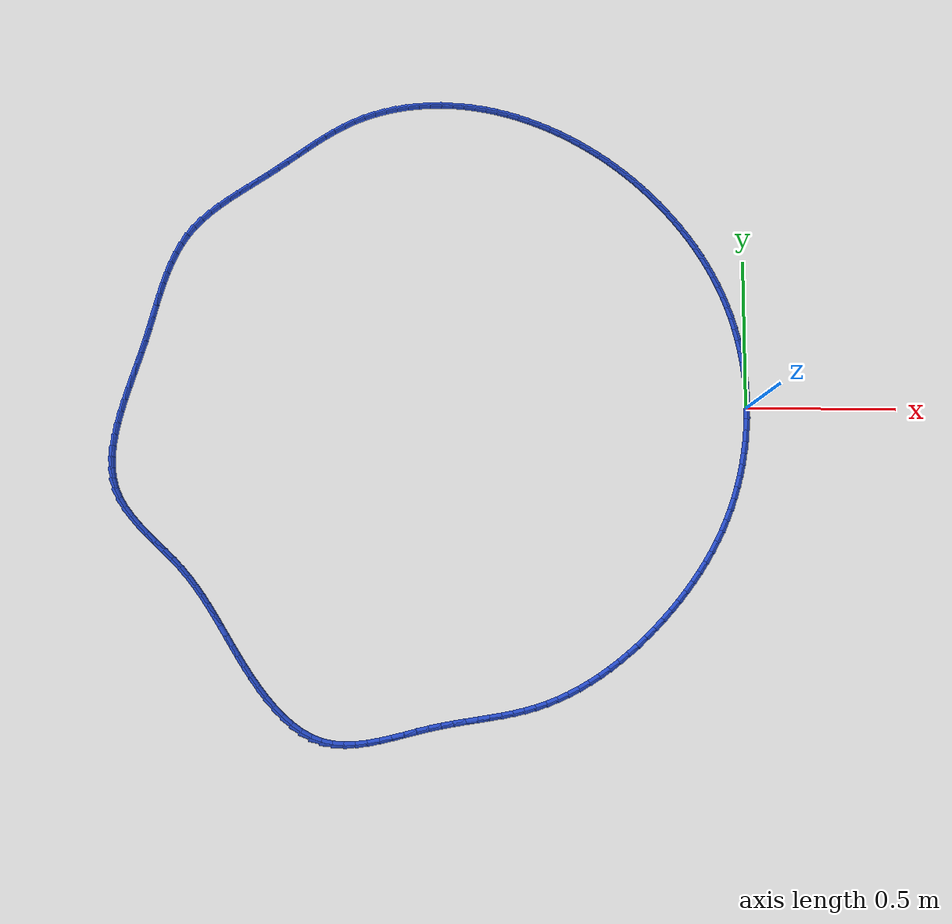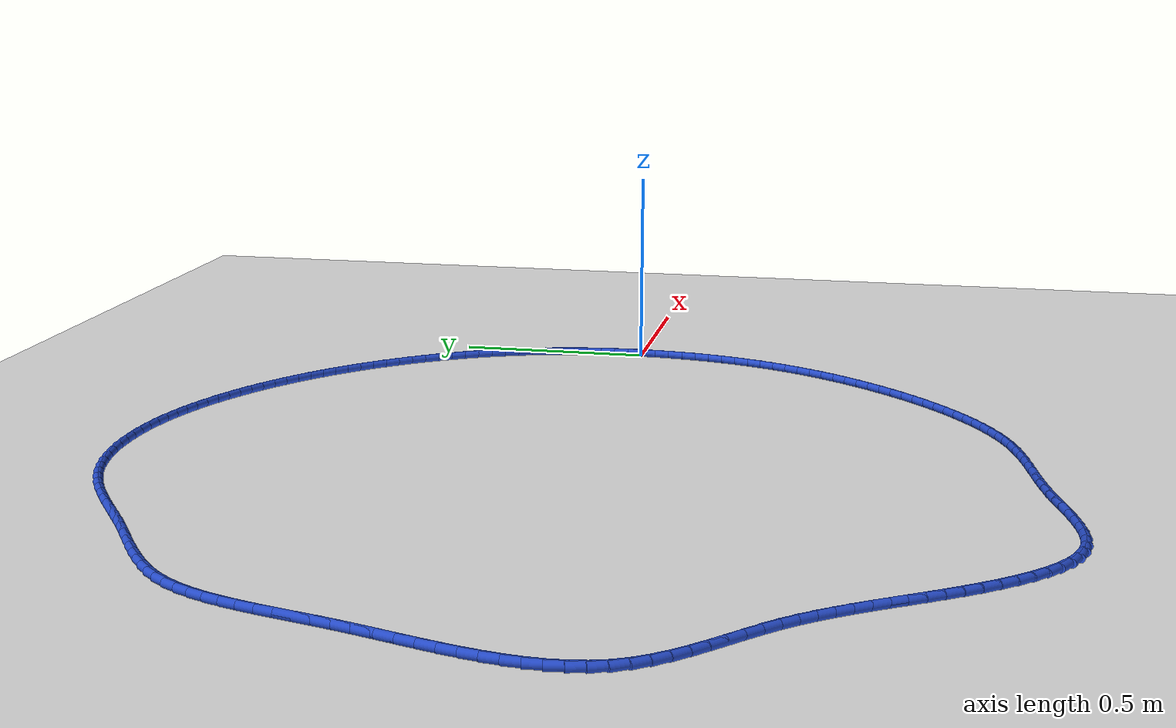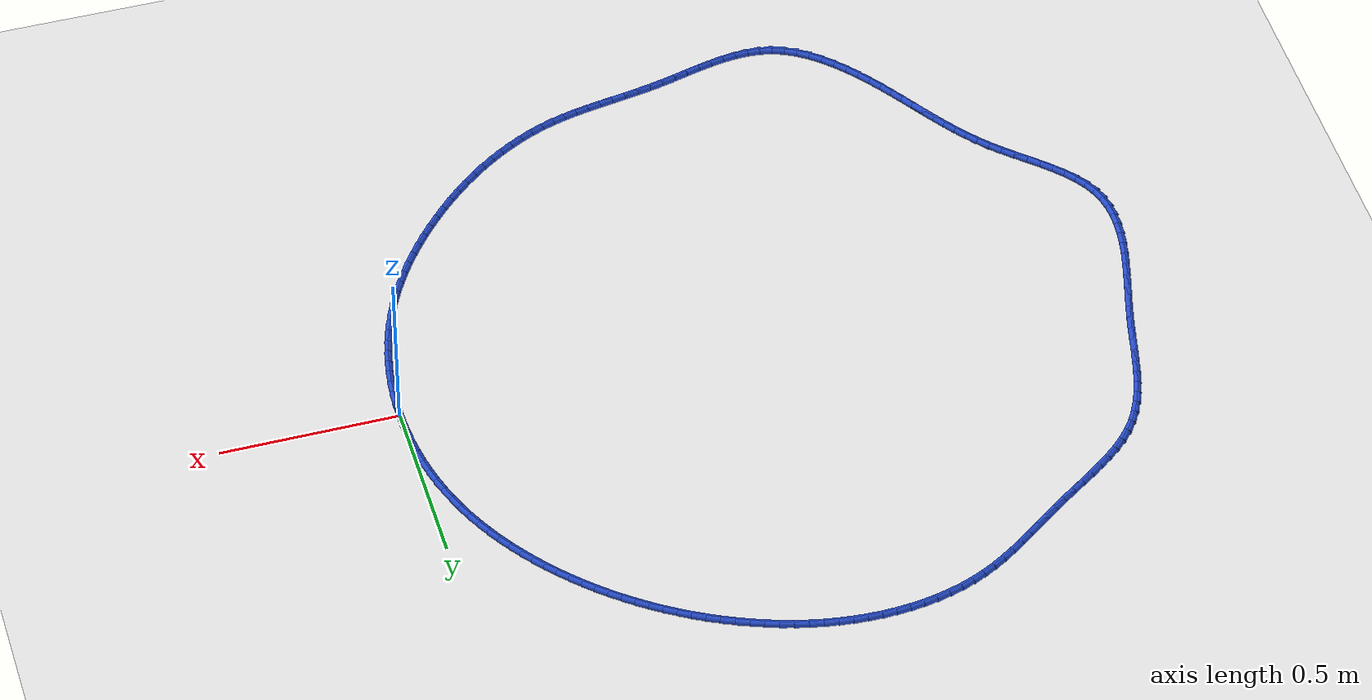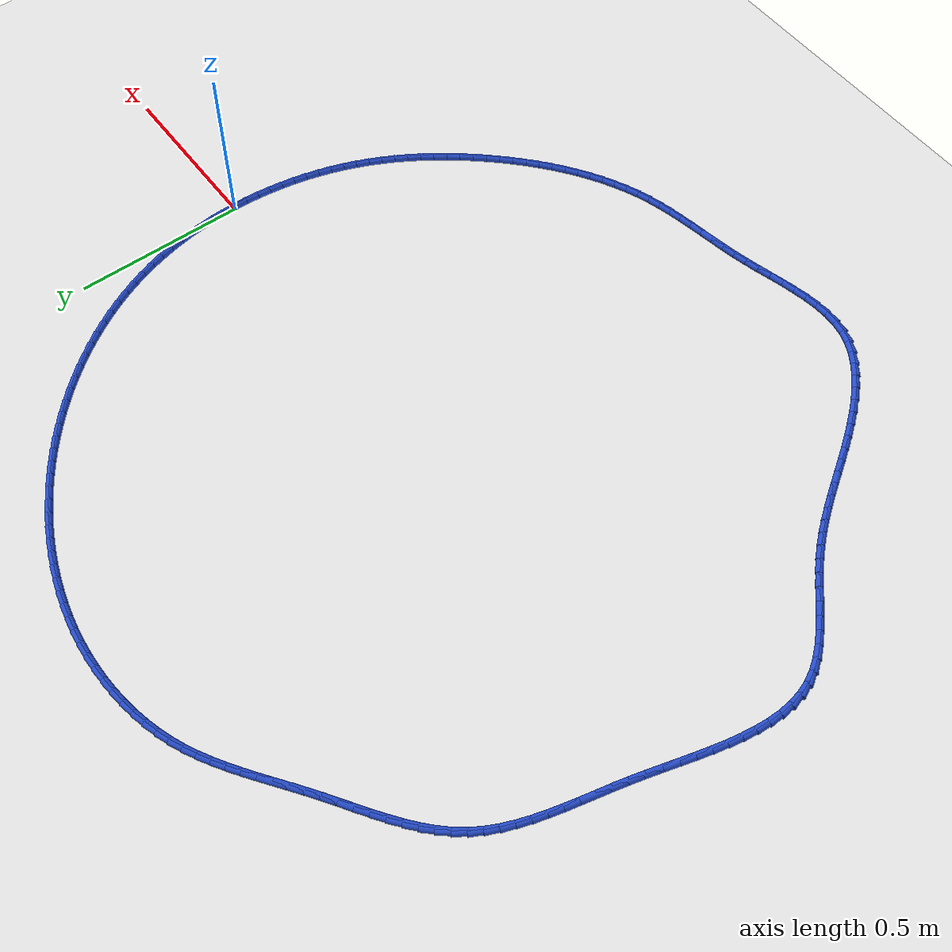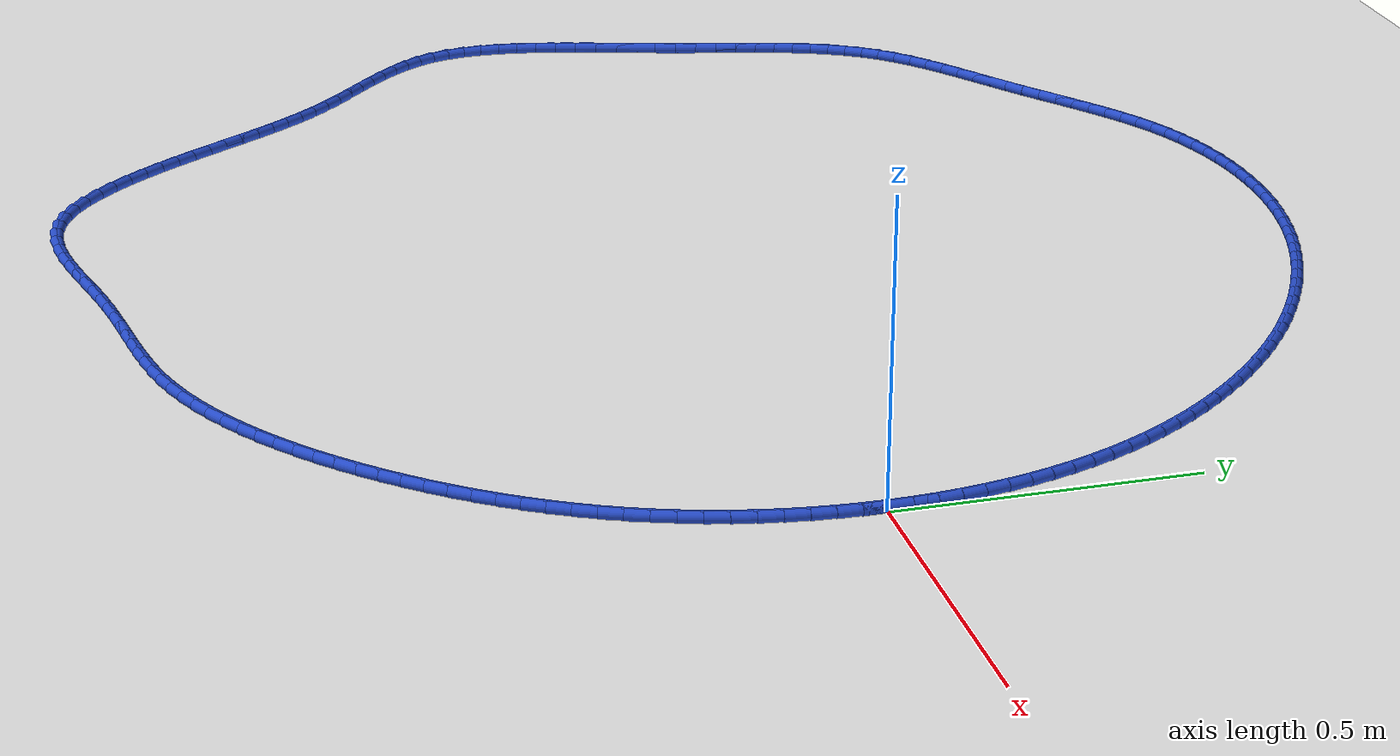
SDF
<sdf version="1.6">
 <world name="default">
  <light name="sun" type="directional">
   <pose>0 0 10 0 -0 0</pose>
   <diffuse>0.8 0.8 0.8 1</diffuse>
   <specular>0.2 0.2 0.2 1</specular>
   <attenuation>
    <range>1000</range>
    <constant>0.9</constant>
    <linear>0.01</linear>
    <quadratic>0.001</quadratic>
   </attenuation>
   <direction>-0.5 0.1 -0.9</direction>
  </light>
  <model name="ground_plane">
   <static>1</static>
   <link name="link">
    <collision name="collision">
     <geometry><plane><normal>0 0 1</normal><size>100 100</size></plane></geometry>
     <surface><friction><ode><mu>100</mu><mu2>50</mu2></ode></friction></surface>
    </collision>
    <visual name="visual">
     <cast_shadows>0</cast_shadows>
     <geometry><plane><normal>0 0 1</normal><size>100 100</size></plane></geometry>
     <material>
      <script><uri>file://media/materials/scripts/gazebo.material</uri><name>Gazebo/WhiteGlow</name></script>
     </material>
    </visual>
   </link>
  </model>
  <gravity>0 0 -9.8</gravity>
  <magnetic_field>6e-06 2.3e-05 -4.2e-05</magnetic_field>
  <atmosphere type="adiabatic"/>
  <physics name="default_physics" default="0" type="ode">
   <max_step_size>0.001</max_step_size>
   <real_time_factor>1</real_time_factor>
   <real_time_update_rate>1000</real_time_update_rate>
  </physics>
  <scene><ambient>0.4 0.4 0.4 1</ambient><background>0.7 0.7 0.7 1</background><shadows>1</shadows></scene>
  <spherical_coordinates>
   <surface_model>EARTH_WGS84</surface_model>
   <latitude_deg>0</latitude_deg>
   <longitude_deg>0</longitude_deg>
   <elevation>0</elevation>
   <heading_deg>0</heading_deg>
  </spherical_coordinates>
  <model name="line">
   <link name="link_0">
    <pose>-8.673617379884035e-19 -3.469446951953614e-17 0.01 0 1.57 -1.5528007192550246</pose>
    <collision name="collision">
     <geometry><cylinder><radius>0.01</radius><length>0.08</length></cylinder></geometry>
    </collision>
    <visual name="visual">
     <material>
      <script><name>Gazebo/Blue</name><uri>file://media/materials/scripts/gazebo.material</uri></script>
     </material>
     <geometry><cylinder><radius>0.01</radius><length>0.08</length></cylinder></geometry>
    </visual>
   </link>
   <link name="link_1">
    <pose>-0.0006976188241995035 0.03876187647245469 0.01 0 1.57 -1.5145606592626306</pose>
    <collision name="collision">
     <geometry><cylinder><radius>0.01</radius><length>0.08</length></cylinder></geometry>
    </collision>
    <visual name="visual">
     <material>
      <script><name>Gazebo/Blue</name><uri>file://media/materials/scripts/gazebo.material</uri></script>
     </material>
     <geometry><cylinder><radius>0.01</radius><length>0.08</length></cylinder></geometry>
    </visual>
   </link>
   <link name="link_2">
    <pose>-0.0028753914818424892 0.07744687070640364 0.01 0 1.57 -1.476112420167916</pose>
    <collision name="collision">
     <geometry><cylinder><radius>0.01</radius><length>0.08</length></cylinder></geometry>
    </collision>
    <visual name="visual">
     <material>
      <script><name>Gazebo/Blue</name><uri>file://media/materials/scripts/gazebo.material</uri></script>
     </material>
     <geometry><cylinder><radius>0.01</radius><length>0.08</length></cylinder></geometry>
    </visual>
   </link>
   <link name="link_3">
    <pose>-0.0065362494007729964 0.11599525331651817 0.01 0 1.57 -1.4373925785867525</pose>
    <collision name="collision">
     <geometry><cylinder><radius>0.01</radius><length>0.08</length></cylinder></geometry>
    </collision>
    <visual name="visual">
     <material>
      <script><name>Gazebo/Blue</name><uri>file://media/materials/scripts/gazebo.material</uri></script>
     </material>
     <geometry><cylinder><radius>0.01</radius><length>0.08</length></cylinder></geometry>
    </visual>
   </link>
   <link name="link_4">
    <pose>-0.01168312400883506 0.15434729491746965 0.01 0 1.57 -1.3983396162019326</pose>
    <collision name="collision">
     <geometry><cylinder><radius>0.01</radius><length>0.08</length></cylinder></geometry>
    </collision>
    <visual name="visual">
     <material>
      <script><name>Gazebo/Blue</name><uri>file://media/materials/scripts/gazebo.material</uri></script>
     </material>
     <geometry><cylinder><radius>0.01</radius><length>0.08</length></cylinder></geometry>
    </visual>
   </link>
   <link name="link_5">
    <pose>-0.01831894673387273 0.19244326612392942 0.01 0 1.57 -1.3588945479753733</pose>
    <collision name="collision">
     <geometry><cylinder><radius>0.01</radius><length>0.08</length></cylinder></geometry>
    </collision>
    <visual name="visual">
     <material>
      <script><name>Gazebo/Blue</name><uri>file://media/materials/scripts/gazebo.material</uri></script>
     </material>
     <geometry><cylinder><radius>0.01</radius><length>0.08</length></cylinder></geometry>
    </visual>
   </link>
   <link name="link_6">
    <pose>-0.02644664900373002 0.23022343755056882 0.01 0 1.57 -1.3190016217012361</pose>
    <collision name="collision">
     <geometry><cylinder><radius>0.01</radius><length>0.08</length></cylinder></geometry>
    </collision>
    <visual name="visual">
     <material>
      <script><name>Gazebo/Blue</name><uri>file://media/materials/scripts/gazebo.material</uri></script>
     </material>
     <geometry><cylinder><radius>0.01</radius><length>0.08</length></cylinder></geometry>
    </visual>
   </link>
   <link name="link_7">
    <pose>-0.036069162246250994 0.26762807981205916 0.01 0 1.57 -1.2786090971801032</pose>
    <collision name="collision">
     <geometry><cylinder><radius>0.01</radius><length>0.08</length></cylinder></geometry>
    </collision>
    <visual name="visual">
     <material>
      <script><name>Gazebo/Blue</name><uri>file://media/materials/scripts/gazebo.material</uri></script>
     </material>
     <geometry><cylinder><radius>0.01</radius><length>0.08</length></cylinder></geometry>
    </visual>
   </link>
   <link name="link_8">
    <pose>-0.04718941788927965 0.30459746352307177 0.01 0 1.57 -1.237670109349435</pose>
    <collision name="collision">
     <geometry><cylinder><radius>0.01</radius><length>0.08</length></cylinder></geometry>
    </collision>
    <visual name="visual">
     <material>
      <script><name>Gazebo/Blue</name><uri>file://media/materials/scripts/gazebo.material</uri></script>
     </material>
     <geometry><cylinder><radius>0.01</radius><length>0.08</length></cylinder></geometry>
    </visual>
   </link>
   <link name="link_9">
    <pose>-0.05981034736066006 0.34107185929827794 0.01 0 1.57 -1.1961686773837916</pose>
    <collision name="collision">
     <geometry><cylinder><radius>0.01</radius><length>0.08</length></cylinder></geometry>
    </collision>
    <visual name="visual">
     <material>
      <script><name>Gazebo/Blue</name><uri>file://media/materials/scripts/gazebo.material</uri></script>
     </material>
     <geometry><cylinder><radius>0.01</radius><length>0.08</length></cylinder></geometry>
    </visual>
   </link>
   <link name="link_10">
    <pose>-0.07393401277643795 0.3769919704398651 0.01 0 1.57 -1.1548489199411496</pose>
    <collision name="collision">
     <geometry><cylinder><radius>0.01</radius><length>0.08</length></cylinder></geometry>
    </collision>
    <visual name="visual">
     <material>
      <script><name>Gazebo/Blue</name><uri>file://media/materials/scripts/gazebo.material</uri></script>
     </material>
     <geometry><cylinder><radius>0.01</radius><length>0.08</length></cylinder></geometry>
    </visual>
   </link>
   <link name="link_11">
    <pose>-0.08953555096275803 0.41231190192802536 0.01 0 1.57 -1.114594249937959</pose>
    <collision name="collision">
     <geometry><cylinder><radius>0.01</radius><length>0.08</length></cylinder></geometry>
    </collision>
    <visual name="visual">
     <material>
      <script><name>Gazebo/Blue</name><uri>file://media/materials/scripts/gazebo.material</uri></script>
     </material>
     <geometry><cylinder><radius>0.01</radius><length>0.08</length></cylinder></geometry>
    </visual>
   </link>
   <link name="link_12">
    <pose>-0.10655864610127636 0.4470014138469582 0.01 0 1.57 -1.0754243051100296</pose>
    <collision name="collision">
     <geometry><cylinder><radius>0.01</radius><length>0.08</length></cylinder></geometry>
    </collision>
    <visual name="visual">
     <material>
      <script><name>Gazebo/Blue</name><uri>file://media/materials/scripts/gazebo.material</uri></script>
     </material>
     <geometry><cylinder><radius>0.01</radius><length>0.08</length></cylinder></geometry>
    </visual>
   </link>
   <link name="link_13">
    <pose>-0.12494520072928447 0.4810311530688671 0.01 0 1.57 -1.03729612925792</pose>
    <collision name="collision">
     <geometry><cylinder><radius>0.01</radius><length>0.08</length></cylinder></geometry>
    </collision>
    <visual name="visual">
     <material>
      <script><name>Gazebo/Blue</name><uri>file://media/materials/scripts/gazebo.material</uri></script>
     </material>
     <geometry><cylinder><radius>0.01</radius><length>0.08</length></cylinder></geometry>
    </visual>
   </link>
   <link name="link_14">
    <pose>-0.14463711738407387 0.5143717664659558 0.01 0 1.57 -1.000157388574682</pose>
    <collision name="collision">
     <geometry><cylinder><radius>0.01</radius><length>0.08</length></cylinder></geometry>
    </collision>
    <visual name="visual">
     <material>
      <script><name>Gazebo/Blue</name><uri>file://media/materials/scripts/gazebo.material</uri></script>
     </material>
     <geometry><cylinder><radius>0.01</radius><length>0.08</length></cylinder></geometry>
    </visual>
   </link>
   <link name="link_15">
    <pose>-0.16557629860293596 0.5469939009104282 0.01 0 1.57 -0.9639480299845541</pose>
    <collision name="collision">
     <geometry><cylinder><radius>0.01</radius><length>0.08</length></cylinder></geometry>
    </collision>
    <visual name="visual">
     <material>
      <script><name>Gazebo/Blue</name><uri>file://media/materials/scripts/gazebo.material</uri></script>
     </material>
     <geometry><cylinder><radius>0.01</radius><length>0.08</length></cylinder></geometry>
    </visual>
   </link>
   <link name="link_16">
    <pose>-0.18770464692316247 0.5788682032744875 0.01 0 1.57 -0.9286017214251387</pose>
    <collision name="collision">
     <geometry><cylinder><radius>0.01</radius><length>0.08</length></cylinder></geometry>
    </collision>
    <visual name="visual">
     <material>
      <script><name>Gazebo/Blue</name><uri>file://media/materials/scripts/gazebo.material</uri></script>
     </material>
     <geometry><cylinder><radius>0.01</radius><length>0.08</length></cylinder></geometry>
    </visual>
   </link>
   <link name="link_17">
    <pose>-0.2109640648820448 0.6099653204303376 0.01 0 1.57 -0.8940470647975035</pose>
    <collision name="collision">
     <geometry><cylinder><radius>0.01</radius><length>0.08</length></cylinder></geometry>
    </collision>
    <visual name="visual">
     <material>
      <script><name>Gazebo/Blue</name><uri>file://media/materials/scripts/gazebo.material</uri></script>
     </material>
     <geometry><cylinder><radius>0.01</radius><length>0.08</length></cylinder></geometry>
    </visual>
   </link>
   <link name="link_18">
    <pose>-0.2352964550168744 0.6402558992501821 0.01 0 1.57 -0.860208584381806</pose>
    <collision name="collision">
     <geometry><cylinder><radius>0.01</radius><length>0.08</length></cylinder></geometry>
    </collision>
    <visual name="visual">
     <material>
      <script><name>Gazebo/Blue</name><uri>file://media/materials/scripts/gazebo.material</uri></script>
     </material>
     <geometry><cylinder><radius>0.01</radius><length>0.08</length></cylinder></geometry>
    </visual>
   </link>
   <link name="link_19">
    <pose>-0.26064371986494284 0.6697105866062247 0.01 0 1.57 -0.8270075016704576</pose>
    <collision name="collision">
     <geometry><cylinder><radius>0.01</radius><length>0.08</length></cylinder></geometry>
    </collision>
    <visual name="visual">
     <material>
      <script><name>Gazebo/Blue</name><uri>file://media/materials/scripts/gazebo.material</uri></script>
     </material>
     <geometry><cylinder><radius>0.01</radius><length>0.08</length></cylinder></geometry>
    </visual>
   </link>
   <link name="link_20">
    <pose>-0.28694776196354177 0.6983000293706688 0.01 0 1.57 -0.7943623125280375</pose>
    <collision name="collision">
     <geometry><cylinder><radius>0.01</radius><length>0.08</length></cylinder></geometry>
    </collision>
    <visual name="visual">
     <material>
      <script><name>Gazebo/Blue</name><uri>file://media/materials/scripts/gazebo.material</uri></script>
     </material>
     <geometry><cylinder><radius>0.01</radius><length>0.08</length></cylinder></geometry>
    </visual>
   </link>
   <link name="link_21">
    <pose>-0.3141504838499626 0.7259948744157183 0.01 0 1.57 -0.7621891850973217</pose>
    <collision name="collision">
     <geometry><cylinder><radius>0.01</radius><length>0.08</length></cylinder></geometry>
    </collision>
    <visual name="visual">
     <material>
      <script><name>Gazebo/Blue</name><uri>file://media/materials/scripts/gazebo.material</uri></script>
     </material>
     <geometry><cylinder><radius>0.01</radius><length>0.08</length></cylinder></geometry>
    </visual>
   </link>
   <link name="link_22">
    <pose>-0.3421937880614966 0.7527657686135767 0.01 0 1.57 -0.7303092666577966</pose>
    <collision name="collision">
     <geometry><cylinder><radius>0.01</radius><length>0.08</length></cylinder></geometry>
    </collision>
    <visual name="visual">
     <material>
      <script><name>Gazebo/Blue</name><uri>file://media/materials/scripts/gazebo.material</uri></script>
     </material>
     <geometry><cylinder><radius>0.01</radius><length>0.08</length></cylinder></geometry>
    </visual>
   </link>
   <link name="link_23">
    <pose>-0.37102613344990376 0.778584402570179 0.01 0 1.57 -0.6982809129060805</pose>
    <collision name="collision">
     <geometry><cylinder><radius>0.01</radius><length>0.08</length></cylinder></geometry>
    </collision>
    <visual name="visual">
     <material>
      <script><name>Gazebo/Blue</name><uri>file://media/materials/scripts/gazebo.material</uri></script>
     </material>
     <geometry><cylinder><radius>0.01</radius><length>0.08</length></cylinder></geometry>
    </visual>
   </link>
   <link name="link_24">
    <pose>-0.40062317583297435 0.803426796517649 0.01 0 1.57 -0.6659943344096472</pose>
    <collision name="collision">
     <geometry><cylinder><radius>0.01</radius><length>0.08</length></cylinder></geometry>
    </collision>
    <visual name="visual">
     <material>
      <script><name>Gazebo/Blue</name><uri>file://media/materials/scripts/gazebo.material</uri></script>
     </material>
     <geometry><cylinder><radius>0.01</radius><length>0.08</length></cylinder></geometry>
    </visual>
   </link>
   <link name="link_25">
    <pose>-0.4309676221308124 0.8272700931896882 0.01 0 1.57 -0.633446040794065</pose>
    <collision name="collision">
     <geometry><cylinder><radius>0.01</radius><length>0.08</length></cylinder></geometry>
    </collision>
    <visual name="visual">
     <material>
      <script><name>Gazebo/Blue</name><uri>file://media/materials/scripts/gazebo.material</uri></script>
     </material>
     <geometry><cylinder><radius>0.01</radius><length>0.08</length></cylinder></geometry>
    </visual>
   </link>
   <link name="link_26">
    <pose>-0.4620421792756493 0.8500914353219275 0.01 0 1.57 -0.6006343960636253</pose>
    <collision name="collision">
     <geometry><cylinder><radius>0.01</radius><length>0.08</length></cylinder></geometry>
    </collision>
    <visual name="visual">
     <material>
      <script><name>Gazebo/Blue</name><uri>file://media/materials/scripts/gazebo.material</uri></script>
     </material>
     <geometry><cylinder><radius>0.01</radius><length>0.08</length></cylinder></geometry>
    </visual>
   </link>
   <link name="link_27">
    <pose>-0.49382955419971564 0.8718679656499986 0.01 0 1.57 -0.5675597928125061</pose>
    <collision name="collision">
     <geometry><cylinder><radius>0.01</radius><length>0.08</length></cylinder></geometry>
    </collision>
    <visual name="visual">
     <material>
      <script><name>Gazebo/Blue</name><uri>file://media/materials/scripts/gazebo.material</uri></script>
     </material>
     <geometry><cylinder><radius>0.01</radius><length>0.08</length></cylinder></geometry>
    </visual>
   </link>
   <link name="link_28">
    <pose>-0.5263124538352428 0.8925768269095327 0.01 0 1.57 -0.5342248180543085</pose>
    <collision name="collision">
     <geometry><cylinder><radius>0.01</radius><length>0.08</length></cylinder></geometry>
    </collision>
    <visual name="visual">
     <material>
      <script><name>Gazebo/Blue</name><uri>file://media/materials/scripts/gazebo.material</uri></script>
     </material>
     <geometry><cylinder><radius>0.01</radius><length>0.08</length></cylinder></geometry>
    </visual>
   </link>
   <link name="link_29">
    <pose>-0.559473585114462 0.9121951618361613 0.01 0 1.57 -0.5006344066107499</pose>
    <collision name="collision">
     <geometry><cylinder><radius>0.01</radius><length>0.08</length></cylinder></geometry>
    </collision>
    <visual name="visual">
     <material>
      <script><name>Gazebo/Blue</name><uri>file://media/materials/scripts/gazebo.material</uri></script>
     </material>
     <geometry><cylinder><radius>0.01</radius><length>0.08</length></cylinder></geometry>
    </visual>
   </link>
   <link name="link_30">
    <pose>-0.5932956549696041 0.9307001131655158 0.01 0 1.57 -0.4667958939564992</pose>
    <collision name="collision">
     <geometry><cylinder><radius>0.01</radius><length>0.08</length></cylinder></geometry>
    </collision>
    <visual name="visual">
     <material>
      <script><name>Gazebo/Blue</name><uri>file://media/materials/scripts/gazebo.material</uri></script>
     </material>
     <geometry><cylinder><radius>0.01</radius><length>0.08</length></cylinder></geometry>
    </visual>
   </link>
   <link name="link_31">
    <pose>-0.6277613672244562 0.948068818441914 0.01 0 1.57 -0.4325614016017076</pose>
    <collision name="collision">
     <geometry><cylinder><radius>0.01</radius><length>0.08</length></cylinder></geometry>
    </collision>
    <visual name="visual">
     <material>
      <script><name>Gazebo/Blue</name><uri>file://media/materials/scripts/gazebo.material</uri></script>
     </material>
     <geometry><cylinder><radius>0.01</radius><length>0.08</length></cylinder></geometry>
    </visual>
   </link>
   <link name="link_32">
    <pose>-0.6628478625673129 0.9642691243940221 0.01 0 1.57 -0.3974134527887569</pose>
    <collision name="collision">
     <geometry><cylinder><radius>0.01</radius><length>0.08</length></cylinder></geometry>
    </collision>
    <visual name="visual">
     <material>
      <script><name>Gazebo/Blue</name><uri>file://media/materials/scripts/gazebo.material</uri></script>
     </material>
     <geometry><cylinder><radius>0.01</radius><length>0.08</length></cylinder></geometry>
    </visual>
   </link>
   <link name="link_33">
    <pose>-0.6985152439205533 0.9792404235195352 0.01 0 1.57 -0.36117393872409154</pose>
    <collision name="collision">
     <geometry><cylinder><radius>0.01</radius><length>0.08</length></cylinder></geometry>
    </collision>
    <visual name="visual">
     <material>
      <script><name>Gazebo/Blue</name><uri>file://media/materials/scripts/gazebo.material</uri></script>
     </material>
     <geometry><cylinder><radius>0.01</radius><length>0.08</length></cylinder></geometry>
    </visual>
   </link>
   <link name="link_34">
    <pose>-0.7347203636186392 0.9929166796126507 0.01 0 1.57 -0.3237586518239457</pose>
    <collision name="collision">
     <geometry><cylinder><radius>0.01</radius><length>0.08</length></cylinder></geometry>
    </collision>
    <visual name="visual">
     <material>
      <script><name>Gazebo/Blue</name><uri>file://media/materials/scripts/gazebo.material</uri></script>
     </material>
     <geometry><cylinder><radius>0.01</radius><length>0.08</length></cylinder></geometry>
    </visual>
   </link>
   <link name="link_35">
    <pose>-0.7714200739960319 1.0052318564675662 0.01 0 1.57 -0.2850912183244753</pose>
    <collision name="collision">
     <geometry><cylinder><radius>0.01</radius><length>0.08</length></cylinder></geometry>
    </collision>
    <visual name="visual">
     <material>
      <script><name>Gazebo/Blue</name><uri>file://media/materials/scripts/gazebo.material</uri></script>
     </material>
     <geometry><cylinder><radius>0.01</radius><length>0.08</length></cylinder></geometry>
    </visual>
   </link>
   <link name="link_36">
    <pose>-0.8085712273871934 1.0161199178784799 0.01 0 1.57 -0.24510514287906918</pose>
    <collision name="collision">
     <geometry><cylinder><radius>0.01</radius><length>0.08</length></cylinder></geometry>
    </collision>
    <visual name="visual">
     <material>
      <script><name>Gazebo/Blue</name><uri>file://media/materials/scripts/gazebo.material</uri></script>
     </material>
     <geometry><cylinder><radius>0.01</radius><length>0.08</length></cylinder></geometry>
    </visual>
   </link>
   <link name="link_37">
    <pose>-0.8461306761265852 1.025514827639589 0.01 0 1.57 -0.20374623582066057</pose>
    <collision name="collision">
     <geometry><cylinder><radius>0.01</radius><length>0.08</length></cylinder></geometry>
    </collision>
    <visual name="visual">
     <material>
      <script><name>Gazebo/Blue</name><uri>file://media/materials/scripts/gazebo.material</uri></script>
     </material>
     <geometry><cylinder><radius>0.01</radius><length>0.08</length></cylinder></geometry>
    </visual>
   </link>
   <link name="link_38">
    <pose>-0.8840552725486686 1.0333505495450916 0.01 0 1.57 -0.16097538476243362</pose>
    <collision name="collision">
     <geometry><cylinder><radius>0.01</radius><length>0.08</length></cylinder></geometry>
    </collision>
    <visual name="visual">
     <material>
      <script><name>Gazebo/Blue</name><uri>file://media/materials/scripts/gazebo.material</uri></script>
     </material>
     <geometry><cylinder><radius>0.01</radius><length>0.08</length></cylinder></geometry>
    </visual>
   </link>
   <link name="link_39">
    <pose>-0.9223018689879054 1.0395610473891852 0.01 0 1.57 -0.11677159319889402</pose>
    <collision name="collision">
     <geometry><cylinder><radius>0.01</radius><length>0.08</length></cylinder></geometry>
    </collision>
    <visual name="visual">
     <material>
      <script><name>Gazebo/Blue</name><uri>file://media/materials/scripts/gazebo.material</uri></script>
     </material>
     <geometry><cylinder><radius>0.01</radius><length>0.08</length></cylinder></geometry>
    </visual>
   </link>
   <link name="link_40">
    <pose>-0.9608273177787579 1.0440802849660684 0.01 0 1.57 -0.07113516022922692</pose>
    <collision name="collision">
     <geometry><cylinder><radius>0.01</radius><length>0.08</length></cylinder></geometry>
    </collision>
    <visual name="visual">
     <material>
      <script><name>Gazebo/Blue</name><uri>file://media/materials/scripts/gazebo.material</uri></script>
     </material>
     <geometry><cylinder><radius>0.01</radius><length>0.08</length></cylinder></geometry>
    </visual>
   </link>
   <link name="link_41">
    <pose>-0.9995884712556866 1.0468422260699377 0.01 0 1.57 -0.02410412454142514</pose>
    <collision name="collision">
     <geometry><cylinder><radius>0.01</radius><length>0.08</length></cylinder></geometry>
    </collision>
    <visual name="visual">
     <material>
      <script><name>Gazebo/Blue</name><uri>file://media/materials/scripts/gazebo.material</uri></script>
     </material>
     <geometry><cylinder><radius>0.01</radius><length>0.08</length></cylinder></geometry>
    </visual>
   </link>
   <link name="link_42">
    <pose>-1.0385401528407097 1.0477813041318849 0.01 0 1.57 0.02397031605829382</pose>
    <collision name="collision">
     <geometry><cylinder><radius>0.01</radius><length>0.08</length></cylinder></geometry>
    </collision>
    <visual name="visual">
     <material>
      <script><name>Gazebo/Blue</name><uri>file://media/materials/scripts/gazebo.material</uri></script>
     </material>
     <geometry><cylinder><radius>0.01</radius><length>0.08</length></cylinder></geometry>
    </visual>
   </link>
   <link name="link_43">
    <pose>-1.0775793356899235 1.0468453433132408 0.01 0 1.57 0.07297727196321811</pose>
    <collision name="collision">
     <geometry><cylinder><radius>0.01</radius><length>0.08</length></cylinder></geometry>
    </collision>
    <visual name="visual">
     <material>
      <script><name>Gazebo/Blue</name><uri>file://media/materials/scripts/gazebo.material</uri></script>
     </material>
     <geometry><cylinder><radius>0.01</radius><length>0.08</length></cylinder></geometry>
    </visual>
   </link>
   <link name="link_44">
    <pose>-1.1165381483093906 1.043997177511281 0.01 0 1.57 0.12329537877361363</pose>
    <collision name="collision">
     <geometry><cylinder><radius>0.01</radius><length>0.08</length></cylinder></geometry>
    </collision>
    <visual name="visual">
     <material>
      <script><name>Gazebo/Blue</name><uri>file://media/materials/scripts/gazebo.material</uri></script>
     </material>
     <geometry><cylinder><radius>0.01</radius><length>0.08</length></cylinder></geometry>
    </visual>
   </link>
   <link name="link_45">
    <pose>-1.1552452857007953 1.039200435384209 0.01 0 1.57 0.17532218516598966</pose>
    <collision name="collision">
     <geometry><cylinder><radius>0.01</radius><length>0.08</length></cylinder></geometry>
    </collision>
    <visual name="visual">
     <material>
      <script><name>Gazebo/Blue</name><uri>file://media/materials/scripts/gazebo.material</uri></script>
     </material>
     <geometry><cylinder><radius>0.01</radius><length>0.08</length></cylinder></geometry>
    </visual>
   </link>
   <link name="link_46">
    <pose>-1.193529442865821 1.0324187455902265 0.01 0 1.57 0.22945096936058504</pose>
    <collision name="collision">
     <geometry><cylinder><radius>0.01</radius><length>0.08</length></cylinder></geometry>
    </collision>
    <visual name="visual">
     <material>
      <script><name>Gazebo/Blue</name><uri>file://media/materials/scripts/gazebo.material</uri></script>
     </material>
     <geometry><cylinder><radius>0.01</radius><length>0.08</length></cylinder></geometry>
    </visual>
   </link>
   <link name="link_47">
    <pose>-1.2312193148061519 1.0236157367875358 0.01 0 1.57 0.28606680354659647</pose>
    <collision name="collision">
     <geometry><cylinder><radius>0.01</radius><length>0.08</length></cylinder></geometry>
    </collision>
    <visual name="visual">
     <material>
      <script><name>Gazebo/Blue</name><uri>file://media/materials/scripts/gazebo.material</uri></script>
     </material>
     <geometry><cylinder><radius>0.01</radius><length>0.08</length></cylinder></geometry>
    </visual>
   </link>
   <link name="link_48">
    <pose>-1.2681435965234715 1.0127550376343397 0.01 0 1.57 0.34553840286568643</pose>
    <collision name="collision">
     <geometry><cylinder><radius>0.01</radius><length>0.08</length></cylinder></geometry>
    </collision>
    <visual name="visual">
     <material>
      <script><name>Gazebo/Blue</name><uri>file://media/materials/scripts/gazebo.material</uri></script>
     </material>
     <geometry><cylinder><radius>0.01</radius><length>0.08</length></cylinder></geometry>
    </visual>
   </link>
   <link name="link_49">
    <pose>-1.3041309830194643 0.9998002767888412 0.01 0 1.57 0.4080485546917933</pose>
    <collision name="collision">
     <geometry><cylinder><radius>0.01</radius><length>0.08</length></cylinder></geometry>
    </collision>
    <visual name="visual">
     <material>
      <script><name>Gazebo/Blue</name><uri>file://media/materials/scripts/gazebo.material</uri></script>
     </material>
     <geometry><cylinder><radius>0.01</radius><length>0.08</length></cylinder></geometry>
    </visual>
   </link>
   <link name="link_50">
    <pose>-1.3390151592330886 0.984719390913751 0.01 0 1.57 0.46855449114741743</pose>
    <collision name="collision">
     <geometry><cylinder><radius>0.01</radius><length>0.08</length></cylinder></geometry>
    </collision>
    <visual name="visual">
     <material>
      <script><name>Gazebo/Blue</name><uri>file://media/materials/scripts/gazebo.material</uri></script>
     </material>
     <geometry><cylinder><radius>0.01</radius><length>0.08</length></cylinder></geometry>
    </visual>
   </link>
   <link name="link_51">
    <pose>-1.3727941498269294 0.9676221974673627 0.01 0 1.57 0.5202995534229727</pose>
    <collision name="collision">
     <geometry><cylinder><radius>0.01</radius><length>0.08</length></cylinder></geometry>
    </collision>
    <visual name="visual">
     <material>
      <script><name>Gazebo/Blue</name><uri>file://media/materials/scripts/gazebo.material</uri></script>
     </material>
     <geometry><cylinder><radius>0.01</radius><length>0.08</length></cylinder></geometry>
    </visual>
   </link>
   <link name="link_52">
    <pose>-1.405663740203178 0.948789248350323 0.01 0 1.57 0.5624614812539859</pose>
    <collision name="collision">
     <geometry><cylinder><radius>0.01</radius><length>0.08</length></cylinder></geometry>
    </collision>
    <visual name="visual">
     <material>
      <script><name>Gazebo/Blue</name><uri>file://media/materials/scripts/gazebo.material</uri></script>
     </material>
     <geometry><cylinder><radius>0.01</radius><length>0.08</length></cylinder></geometry>
    </visual>
   </link>
   <link name="link_53">
    <pose>-1.437831461794479 0.9285112362625276 0.01 0 1.57 0.594895043751565</pose>
    <collision name="collision">
     <geometry><cylinder><radius>0.01</radius><length>0.08</length></cylinder></geometry>
    </collision>
    <visual name="visual">
     <material>
      <script><name>Gazebo/Blue</name><uri>file://media/materials/scripts/gazebo.material</uri></script>
     </material>
     <geometry><cylinder><radius>0.01</radius><length>0.08</length></cylinder></geometry>
    </visual>
   </link>
   <link name="link_54">
    <pose>-1.4695048460334779 0.9070788539038704 0.01 0 1.57 0.617651340984811</pose>
    <collision name="collision">
     <geometry><cylinder><radius>0.01</radius><length>0.08</length></cylinder></geometry>
    </collision>
    <visual name="visual">
     <material>
      <script><name>Gazebo/Blue</name><uri>file://media/materials/scripts/gazebo.material</uri></script>
     </material>
     <geometry><cylinder><radius>0.01</radius><length>0.08</length></cylinder></geometry>
    </visual>
   </link>
   <link name="link_55">
    <pose>-1.500891424352818 0.8847827939742459 0.01 0 1.57 0.630884267205893</pose>
    <collision name="collision">
     <geometry><cylinder><radius>0.01</radius><length>0.08</length></cylinder></geometry>
    </collision>
    <visual name="visual">
     <material>
      <script><name>Gazebo/Blue</name><uri>file://media/materials/scripts/gazebo.material</uri></script>
     </material>
     <geometry><cylinder><radius>0.01</radius><length>0.08</length></cylinder></geometry>
    </visual>
   </link>
   <link name="link_56">
    <pose>-1.5321987281851455 0.8619137491735495 0.01 0 1.57 0.6347853095381931</pose>
    <collision name="collision">
     <geometry><cylinder><radius>0.01</radius><length>0.08</length></cylinder></geometry>
    </collision>
    <visual name="visual">
     <material>
      <script><name>Gazebo/Blue</name><uri>file://media/materials/scripts/gazebo.material</uri></script>
     </material>
     <geometry><cylinder><radius>0.01</radius><length>0.08</length></cylinder></geometry>
    </visual>
   </link>
   <link name="link_57">
    <pose>-1.563634288963104 0.8387624122016755 0.01 0 1.57 0.6295472895425105</pose>
    <collision name="collision">
     <geometry><cylinder><radius>0.01</radius><length>0.08</length></cylinder></geometry>
    </collision>
    <visual name="visual">
     <material>
      <script><name>Gazebo/Blue</name><uri>file://media/materials/scripts/gazebo.material</uri></script>
     </material>
     <geometry><cylinder><radius>0.01</radius><length>0.08</length></cylinder></geometry>
    </visual>
   </link>
   <link name="link_58">
    <pose>-1.59540563811934 0.8156194757585186 0.01 0 1.57 0.6153993894372117</pose>
    <collision name="collision">
     <geometry><cylinder><radius>0.01</radius><length>0.08</length></cylinder></geometry>
    </collision>
    <visual name="visual">
     <material>
      <script><name>Gazebo/Blue</name><uri>file://media/materials/scripts/gazebo.material</uri></script>
     </material>
     <geometry><cylinder><radius>0.01</radius><length>0.08</length></cylinder></geometry>
    </visual>
   </link>
   <link name="link_59">
    <pose>-1.6277189389205615 0.7927744144876836 0.01 0 1.57 0.598895487060055</pose>
    <collision name="collision">
     <geometry><cylinder><radius>0.01</radius><length>0.08</length></cylinder></geometry>
    </collision>
    <visual name="visual">
     <material>
      <script><name>Gazebo/Blue</name><uri>file://media/materials/scripts/gazebo.material</uri></script>
     </material>
     <geometry><cylinder><radius>0.01</radius><length>0.08</length></cylinder></geometry>
    </visual>
   </link>
   <link name="link_60">
    <pose>-1.6605850010427132 0.770342782849543 0.01 0 1.57 0.5928847009661464</pose>
    <collision name="collision">
     <geometry><cylinder><radius>0.01</radius><length>0.08</length></cylinder></geometry>
    </collision>
    <visual name="visual">
     <material>
      <script><name>Gazebo/Blue</name><uri>file://media/materials/scripts/gazebo.material</uri></script>
     </material>
     <geometry><cylinder><radius>0.01</radius><length>0.08</length></cylinder></geometry>
    </visual>
   </link>
   <link name="link_61">
    <pose>-1.6936180362979594 0.7480870505576414 0.01 0 1.57 0.598826889611957</pose>
    <collision name="collision">
     <geometry><cylinder><radius>0.01</radius><length>0.08</length></cylinder></geometry>
    </collision>
    <visual name="visual">
     <material>
      <script><name>Gazebo/Blue</name><uri>file://media/materials/scripts/gazebo.material</uri></script>
     </material>
     <geometry><cylinder><radius>0.01</radius><length>0.08</length></cylinder></geometry>
    </visual>
   </link>
   <link name="link_62">
    <pose>-1.7263841951715537 0.7257268990934262 0.01 0 1.57 0.6169585502910816</pose>
    <collision name="collision">
     <geometry><cylinder><radius>0.01</radius><length>0.08</length></cylinder></geometry>
    </collision>
    <visual name="visual">
     <material>
      <script><name>Gazebo/Blue</name><uri>file://media/materials/scripts/gazebo.material</uri></script>
     </material>
     <geometry><cylinder><radius>0.01</radius><length>0.08</length></cylinder></geometry>
    </visual>
   </link>
   <link name="link_63">
    <pose>-1.7584496281487514 0.7029820099383466 0.01 0 1.57 0.6478691887304979</pose>
    <collision name="collision">
     <geometry><cylinder><radius>0.01</radius><length>0.08</length></cylinder></geometry>
    </collision>
    <visual name="visual">
     <material>
      <script><name>Gazebo/Blue</name><uri>file://media/materials/scripts/gazebo.material</uri></script>
     </material>
     <geometry><cylinder><radius>0.01</radius><length>0.08</length></cylinder></geometry>
    </visual>
   </link>
   <link name="link_64">
    <pose>-1.7893804857148055 0.6795720645738502 0.01 0 1.57 0.692455212820586</pose>
    <collision name="collision">
     <geometry><cylinder><radius>0.01</radius><length>0.08</length></cylinder></geometry>
    </collision>
    <visual name="visual">
     <material>
      <script><name>Gazebo/Blue</name><uri>file://media/materials/scripts/gazebo.material</uri></script>
     </material>
     <geometry><cylinder><radius>0.01</radius><length>0.08</length></cylinder></geometry>
    </visual>
   </link>
   <link name="link_65">
    <pose>-1.8187429183549715 0.655216744481386 0.01 0 1.57 0.7518047333218207</pose>
    <collision name="collision">
     <geometry><cylinder><radius>0.01</radius><length>0.08</length></cylinder></geometry>
    </collision>
    <visual name="visual">
     <material>
      <script><name>Gazebo/Blue</name><uri>file://media/materials/scripts/gazebo.material</uri></script>
     </material>
     <geometry><cylinder><radius>0.01</radius><length>0.08</length></cylinder></geometry>
    </visual>
   </link>
   <link name="link_66">
    <pose>-1.8461030765545035 0.6296357311424017 0.01 0 1.57 0.8269613467392573</pose>
    <collision name="collision">
     <geometry><cylinder><radius>0.01</radius><length>0.08</length></cylinder></geometry>
    </collision>
    <visual name="visual">
     <material>
      <script><name>Gazebo/Blue</name><uri>file://media/materials/scripts/gazebo.material</uri></script>
     </material>
     <geometry><cylinder><radius>0.01</radius><length>0.08</length></cylinder></geometry>
    </visual>
   </link>
   <link name="link_67">
    <pose>-1.871027110798656 0.602548706038346 0.01 0 1.57 0.9180808549782101</pose>
    <collision name="collision">
     <geometry><cylinder><radius>0.01</radius><length>0.08</length></cylinder></geometry>
    </collision>
    <visual name="visual">
     <material>
      <script><name>Gazebo/Blue</name><uri>file://media/materials/scripts/gazebo.material</uri></script>
     </material>
     <geometry><cylinder><radius>0.01</radius><length>0.08</length></cylinder></geometry>
    </visual>
   </link>
   <link name="link_68">
    <pose>-1.8930950445692258 0.5736827934199789 0.01 0 1.57 1.012942485640615</pose>
    <collision name="collision">
     <geometry><cylinder><radius>0.01</radius><length>0.08</length></cylinder></geometry>
    </collision>
    <visual name="visual">
     <material>
      <script><name>Gazebo/Blue</name><uri>file://media/materials/scripts/gazebo.material</uri></script>
     </material>
     <geometry><cylinder><radius>0.01</radius><length>0.08</length></cylinder></geometry>
    </visual>
   </link>
   <link name="link_69">
    <pose>-1.9122612434287372 0.5429659495459158 0.01 0 1.57 1.0969310419946503</pose>
    <collision name="collision">
     <geometry><cylinder><radius>0.01</radius><length>0.08</length></cylinder></geometry>
    </collision>
    <visual name="visual">
     <material>
      <script><name>Gazebo/Blue</name><uri>file://media/materials/scripts/gazebo.material</uri></script>
     </material>
     <geometry><cylinder><radius>0.01</radius><length>0.08</length></cylinder></geometry>
    </visual>
   </link>
   <link name="link_70">
    <pose>-1.9288879626675528 0.510544960769603 0.01 0 1.57 1.1680783631220166</pose>
    <collision name="collision">
     <geometry><cylinder><radius>0.01</radius><length>0.08</length></cylinder></geometry>
    </collision>
    <visual name="visual">
     <material>
      <script><name>Gazebo/Blue</name><uri>file://media/materials/scripts/gazebo.material</uri></script>
     </material>
     <geometry><cylinder><radius>0.01</radius><length>0.08</length></cylinder></geometry>
    </visual>
   </link>
   <link name="link_71">
    <pose>-1.943358055599255 0.47657766414536734 0.01 0 1.57 1.2260361169872203</pose>
    <collision name="collision">
     <geometry><cylinder><radius>0.01</radius><length>0.08</length></cylinder></geometry>
    </collision>
    <visual name="visual">
     <material>
      <script><name>Gazebo/Blue</name><uri>file://media/materials/scripts/gazebo.material</uri></script>
     </material>
     <geometry><cylinder><radius>0.01</radius><length>0.08</length></cylinder></geometry>
    </visual>
   </link>
   <link name="link_72">
    <pose>-1.9560543755374258 0.4412218967275364 0.01 0 1.57 1.2710981926636002</pose>
    <collision name="collision">
     <geometry><cylinder><radius>0.01</radius><length>0.08</length></cylinder></geometry>
    </collision>
    <visual name="visual">
     <material>
      <script><name>Gazebo/Blue</name><uri>file://media/materials/scripts/gazebo.material</uri></script>
     </material>
     <geometry><cylinder><radius>0.01</radius><length>0.08</length></cylinder></geometry>
    </visual>
   </link>
   <link name="link_73">
    <pose>-1.9673597757956456 0.40463549557043643 0.01 0 1.57 1.3038858844427896</pose>
    <collision name="collision">
     <geometry><cylinder><radius>0.01</radius><length>0.08</length></cylinder></geometry>
    </collision>
    <visual name="visual">
     <material>
      <script><name>Gazebo/Blue</name><uri>file://media/materials/scripts/gazebo.material</uri></script>
     </material>
     <geometry><cylinder><radius>0.01</radius><length>0.08</length></cylinder></geometry>
    </visual>
   </link>
   <link name="link_74">
    <pose>-1.9776571096874984 0.36697629772839435 0.01 0 1.57 1.3251204218791088</pose>
    <collision name="collision">
     <geometry><cylinder><radius>0.01</radius><length>0.08</length></cylinder></geometry>
    </collision>
    <visual name="visual">
     <material>
      <script><name>Gazebo/Blue</name><uri>file://media/materials/scripts/gazebo.material</uri></script>
     </material>
     <geometry><cylinder><radius>0.01</radius><length>0.08</length></cylinder></geometry>
    </visual>
   </link>
   <link name="link_75">
    <pose>-1.9873292305265657 0.3284021402557378 0.01 0 1.57 1.3354856590196138</pose>
    <collision name="collision">
     <geometry><cylinder><radius>0.01</radius><length>0.08</length></cylinder></geometry>
    </collision>
    <visual name="visual">
     <material>
      <script><name>Gazebo/Blue</name><uri>file://media/materials/scripts/gazebo.material</uri></script>
     </material>
     <geometry><cylinder><radius>0.01</radius><length>0.08</length></cylinder></geometry>
    </visual>
   </link>
   <link name="link_76">
    <pose>-1.9967589916264286 0.2890708602067929 0.01 0 1.57 1.3355611225246233</pose>
    <collision name="collision">
     <geometry><cylinder><radius>0.01</radius><length>0.08</length></cylinder></geometry>
    </collision>
    <visual name="visual">
     <material>
      <script><name>Gazebo/Blue</name><uri>file://media/materials/scripts/gazebo.material</uri></script>
     </material>
     <geometry><cylinder><radius>0.01</radius><length>0.08</length></cylinder></geometry>
    </visual>
   </link>
   <link name="link_77">
    <pose>-2.0063292463006692 0.24914029463588658 0.01 0 1.57 1.3258037215584941</pose>
    <collision name="collision">
     <geometry><cylinder><radius>0.01</radius><length>0.08</length></cylinder></geometry>
    </collision>
    <visual name="visual">
     <material>
      <script><name>Gazebo/Blue</name><uri>file://media/materials/scripts/gazebo.material</uri></script>
     </material>
     <geometry><cylinder><radius>0.01</radius><length>0.08</length></cylinder></geometry>
    </visual>
   </link>
   <link name="link_78">
    <pose>-2.016422847862871 0.20876828059734645 0.01 0 1.57 1.3076866216361704</pose>
    <collision name="collision">
     <geometry><cylinder><radius>0.01</radius><length>0.08</length></cylinder></geometry>
    </collision>
    <visual name="visual">
     <material>
      <script><name>Gazebo/Blue</name><uri>file://media/materials/scripts/gazebo.material</uri></script>
     </material>
     <geometry><cylinder><radius>0.01</radius><length>0.08</length></cylinder></geometry>
    </visual>
   </link>
   <link name="link_79">
    <pose>-2.0273739212579844 0.16811148646692367 0.01 0 1.57 1.2926458032368067</pose>
    <collision name="collision">
     <geometry><cylinder><radius>0.01</radius><length>0.08</length></cylinder></geometry>
    </collision>
    <visual name="visual">
     <material>
      <script><name>Gazebo/Blue</name><uri>file://media/materials/scripts/gazebo.material</uri></script>
     </material>
     <geometry><cylinder><radius>0.01</radius><length>0.08</length></cylinder></geometry>
    </visual>
   </link>
   <link name="link_80">
    <pose>-2.0390235494092726 0.1273147557293781 0.01 0 1.57 1.2869283241136418</pose>
    <collision name="collision">
     <geometry><cylinder><radius>0.01</radius><length>0.08</length></cylinder></geometry>
    </collision>
    <visual name="visual">
     <material>
      <script><name>Gazebo/Blue</name><uri>file://media/materials/scripts/gazebo.material</uri></script>
     </material>
     <geometry><cylinder><radius>0.01</radius><length>0.08</length></cylinder></geometry>
    </visual>
   </link>
   <link name="link_81">
    <pose>-2.050926439249759 0.08651606356064598 0.01 0 1.57 1.290465317721703</pose>
    <collision name="collision">
     <geometry><cylinder><radius>0.01</radius><length>0.08</length></cylinder></geometry>
    </collision>
    <visual name="visual">
     <material>
      <script><name>Gazebo/Blue</name><uri>file://media/materials/scripts/gazebo.material</uri></script>
     </material>
     <geometry><cylinder><radius>0.01</radius><length>0.08</length></cylinder></geometry>
    </visual>
   </link>
   <link name="link_82">
    <pose>-2.062633766761956 0.045853300451985414 0.01 0 1.57 1.303443632524193</pose>
    <collision name="collision">
     <geometry><cylinder><radius>0.01</radius><length>0.08</length></cylinder></geometry>
    </collision>
    <visual name="visual">
     <material>
      <script><name>Gazebo/Blue</name><uri>file://media/materials/scripts/gazebo.material</uri></script>
     </material>
     <geometry><cylinder><radius>0.01</radius><length>0.08</length></cylinder></geometry>
    </visual>
   </link>
   <link name="link_83">
    <pose>-2.073696707928377 0.005464356894655555 0.01 0 1.57 1.3263963725436894</pose>
    <collision name="collision">
     <geometry><cylinder><radius>0.01</radius><length>0.08</length></cylinder></geometry>
    </collision>
    <visual name="visual">
     <material>
      <script><name>Gazebo/Blue</name><uri>file://media/materials/scripts/gazebo.material</uri></script>
     </material>
     <geometry><cylinder><radius>0.01</radius><length>0.08</length></cylinder></geometry>
    </visual>
   </link>
   <link name="link_84">
    <pose>-2.0836664387315333 -0.03451287662008594 0.01 0 1.57 1.3602142777690576</pose>
    <collision name="collision">
     <geometry><cylinder><radius>0.01</radius><length>0.08</length></cylinder></geometry>
    </collision>
    <visual name="visual">
     <material>
      <script><name>Gazebo/Blue</name><uri>file://media/materials/scripts/gazebo.material</uri></script>
     </material>
     <geometry><cylinder><radius>0.01</radius><length>0.08</length></cylinder></geometry>
    </visual>
   </link>
   <link name="link_85">
    <pose>-2.092094135153938 -0.07394050960097981 0.01 0 1.57 1.4061462886673595</pose>
    <collision name="collision">
     <geometry><cylinder><radius>0.01</radius><length>0.08</length></cylinder></geometry>
    </collision>
    <visual name="visual">
     <material>
      <script><name>Gazebo/Blue</name><uri>file://media/materials/scripts/gazebo.material</uri></script>
     </material>
     <geometry><cylinder><radius>0.01</radius><length>0.08</length></cylinder></geometry>
    </visual>
   </link>
   <link name="link_86">
    <pose>-2.0985309731781037 -0.11268065155676804 0.01 0 1.57 1.4657595312341334</pose>
    <collision name="collision">
     <geometry><cylinder><radius>0.01</radius><length>0.08</length></cylinder></geometry>
    </collision>
    <visual name="visual">
     <material>
      <script><name>Gazebo/Blue</name><uri>file://media/materials/scripts/gazebo.material</uri></script>
     </material>
     <geometry><cylinder><radius>0.01</radius><length>0.08</length></cylinder></geometry>
    </visual>
   </link>
   <link name="link_87">
    <pose>-2.1025281287865427 -0.1505954119961922 0.01 0 1.57 1.5408024958468327</pose>
    <collision name="collision">
     <geometry><cylinder><radius>0.01</radius><length>0.08</length></cylinder></geometry>
    </collision>
    <visual name="visual">
     <material>
      <script><name>Gazebo/Blue</name><uri>file://media/materials/scripts/gazebo.material</uri></script>
     </material>
     <geometry><cylinder><radius>0.01</radius><length>0.08</length></cylinder></geometry>
    </visual>
   </link>
   <link name="link_88">
    <pose>-2.103636777961767 -0.18754690042799382 0.01 0 1.57 -1.5087099486330144</pose>
    <collision name="collision">
     <geometry><cylinder><radius>0.01</radius><length>0.08</length></cylinder></geometry>
    </collision>
    <visual name="visual">
     <material>
      <script><name>Gazebo/Blue</name><uri>file://media/materials/scripts/gazebo.material</uri></script>
     </material>
     <geometry><cylinder><radius>0.01</radius><length>0.08</length></cylinder></geometry>
    </visual>
   </link>
   <link name="link_89">
    <pose>-2.10140809668629 -0.22339722636091514 0.01 0 1.57 -1.3987321642752282</pose>
    <collision name="collision">
     <geometry><cylinder><radius>0.01</radius><length>0.08</length></cylinder></geometry>
    </collision>
    <visual name="visual">
     <material>
      <script><name>Gazebo/Blue</name><uri>file://media/materials/scripts/gazebo.material</uri></script>
     </material>
     <geometry><cylinder><radius>0.01</radius><length>0.08</length></cylinder></geometry>
    </visual>
   </link>
   <link name="link_90">
    <pose>-2.0953932609426227 -0.2580084993036964 0.01 0 1.57 -1.271641502561442</pose>
    <collision name="collision">
     <geometry><cylinder><radius>0.01</radius><length>0.08</length></cylinder></geometry>
    </collision>
    <visual name="visual">
     <material>
      <script><name>Gazebo/Blue</name><uri>file://media/materials/scripts/gazebo.material</uri></script>
     </material>
     <geometry><cylinder><radius>0.01</radius><length>0.08</length></cylinder></geometry>
    </visual>
   </link>
   <link name="link_91">
    <pose>-2.085143446713278 -0.2912428287650798 0.01 0 1.57 -1.1316368505930325</pose>
    <collision name="collision">
     <geometry><cylinder><radius>0.01</radius><length>0.08</length></cylinder></geometry>
    </collision>
    <visual name="visual">
     <material>
      <script><name>Gazebo/Blue</name><uri>file://media/materials/scripts/gazebo.material</uri></script>
     </material>
     <geometry><cylinder><radius>0.01</radius><length>0.08</length></cylinder></geometry>
    </visual>
   </link>
   <link name="link_92">
    <pose>-2.0702385947284654 -0.32297187878285166 0.01 0 1.57 -1.0021444335566447</pose>
    <collision name="collision">
     <geometry><cylinder><radius>0.01</radius><length>0.08</length></cylinder></geometry>
    </collision>
    <visual name="visual">
     <material>
      <script><name>Gazebo/Blue</name><uri>file://media/materials/scripts/gazebo.material</uri></script>
     </material>
     <geometry><cylinder><radius>0.01</radius><length>0.08</length></cylinder></geometry>
    </visual>
   </link>
   <link name="link_93">
    <pose>-2.0508747714278206 -0.3532719663626642 0.01 0 1.57 -0.9019492129944634</pose>
    <collision name="collision">
     <geometry><cylinder><radius>0.01</radius><length>0.08</length></cylinder></geometry>
    </collision>
    <visual name="visual">
     <material>
      <script><name>Gazebo/Blue</name><uri>file://media/materials/scripts/gazebo.material</uri></script>
     </material>
     <geometry><cylinder><radius>0.01</radius><length>0.08</length></cylinder></geometry>
    </visual>
   </link>
   <link name="link_94">
    <pose>-2.0278399223450356 -0.38241600769660705 0.01 0 1.57 -0.8292163314461563</pose>
    <collision name="collision">
     <geometry><cylinder><radius>0.01</radius><length>0.08</length></cylinder></geometry>
    </collision>
    <visual name="visual">
     <material>
      <script><name>Gazebo/Blue</name><uri>file://media/materials/scripts/gazebo.material</uri></script>
     </material>
     <geometry><cylinder><radius>0.01</radius><length>0.08</length></cylinder></geometry>
    </visual>
   </link>
   <link name="link_95">
    <pose>-2.001945905987909 -0.41068486193556025 0.01 0 1.57 -0.7806010277706479</pose>
    <collision name="collision">
     <geometry><cylinder><radius>0.01</radius><length>0.08</length></cylinder></geometry>
    </collision>
    <visual name="visual">
     <material>
      <script><name>Gazebo/Blue</name><uri>file://media/materials/scripts/gazebo.material</uri></script>
     </material>
     <geometry><cylinder><radius>0.01</radius><length>0.08</length></cylinder></geometry>
    </visual>
   </link>
   <link name="link_96">
    <pose>-1.9740045808642352 -0.43835938823040577 0.01 0 1.57 -0.7532941024010847</pose>
    <collision name="collision">
     <geometry><cylinder><radius>0.01</radius><length>0.08</length></cylinder></geometry>
    </collision>
    <visual name="visual">
     <material>
      <script><name>Gazebo/Blue</name><uri>file://media/materials/scripts/gazebo.material</uri></script>
     </material>
     <geometry><cylinder><radius>0.01</radius><length>0.08</length></cylinder></geometry>
    </visual>
   </link>
   <link name="link_97">
    <pose>-1.944827805481812 -0.4657204457320249 0.01 0 1.57 -0.7455112572962542</pose>
    <collision name="collision">
     <geometry><cylinder><radius>0.01</radius><length>0.08</length></cylinder></geometry>
    </collision>
    <visual name="visual">
     <material>
      <script><name>Gazebo/Blue</name><uri>file://media/materials/scripts/gazebo.material</uri></script>
     </material>
     <geometry><cylinder><radius>0.01</radius><length>0.08</length></cylinder></geometry>
    </visual>
   </link>
   <link name="link_98">
    <pose>-1.9152274383484362 -0.49304889359129905 0.01 0 1.57 -0.7566081342808237</pose>
    <collision name="collision">
     <geometry><cylinder><radius>0.01</radius><length>0.08</length></cylinder></geometry>
    </collision>
    <visual name="visual">
     <material>
      <script><name>Gazebo/Blue</name><uri>file://media/materials/scripts/gazebo.material</uri></script>
     </material>
     <geometry><cylinder><radius>0.01</radius><length>0.08</length></cylinder></geometry>
    </visual>
   </link>
   <link name="link_99">
    <pose>-1.8860153379719027 -0.5206255909591101 0.01 0 1.57 -0.7870701972161407</pose>
    <collision name="collision">
     <geometry><cylinder><radius>0.01</radius><length>0.08</length></cylinder></geometry>
    </collision>
    <visual name="visual">
     <material>
      <script><name>Gazebo/Blue</name><uri>file://media/materials/scripts/gazebo.material</uri></script>
     </material>
     <geometry><cylinder><radius>0.01</radius><length>0.08</length></cylinder></geometry>
    </visual>
   </link>
   <link name="link_100">
    <pose>-1.85800336286001 -0.5487313969863382 0.01 0 1.57 -0.8341152993728045</pose>
    <collision name="collision">
     <geometry><cylinder><radius>0.01</radius><length>0.08</length></cylinder></geometry>
    </collision>
    <visual name="visual">
     <material>
      <script><name>Gazebo/Blue</name><uri>file://media/materials/scripts/gazebo.material</uri></script>
     </material>
     <geometry><cylinder><radius>0.01</radius><length>0.08</length></cylinder></geometry>
    </visual>
   </link>
   <link name="link_101">
    <pose>-1.8318273377142265 -0.5775907092874687 0.01 0 1.57 -0.8802436031744733</pose>
    <collision name="collision">
     <geometry><cylinder><radius>0.01</radius><length>0.08</length></cylinder></geometry>
    </collision>
    <visual name="visual">
     <material>
      <script><name>Gazebo/Blue</name><uri>file://media/materials/scripts/gazebo.material</uri></script>
     </material>
     <geometry><cylinder><radius>0.01</radius><length>0.08</length></cylinder></geometry>
    </visual>
   </link>
   <link name="link_102">
    <pose>-1.8073727270883366 -0.6071872530307497 0.01 0 1.57 -0.9197733979084806</pose>
    <collision name="collision">
     <geometry><cylinder><radius>0.01</radius><length>0.08</length></cylinder></geometry>
    </collision>
    <visual name="visual">
     <material>
      <script><name>Gazebo/Blue</name><uri>file://media/materials/scripts/gazebo.material</uri></script>
     </material>
     <geometry><cylinder><radius>0.01</radius><length>0.08</length></cylinder></geometry>
    </visual>
   </link>
   <link name="link_103">
    <pose>-1.7843251005947074 -0.6374406385661127 0.01 0 1.57 -0.9519709376212624</pose>
    <collision name="collision">
     <geometry><cylinder><radius>0.01</radius><length>0.08</length></cylinder></geometry>
    </collision>
    <visual name="visual">
     <material>
      <script><name>Gazebo/Blue</name><uri>file://media/materials/scripts/gazebo.material</uri></script>
     </material>
     <geometry><cylinder><radius>0.01</radius><length>0.08</length></cylinder></geometry>
    </visual>
   </link>
   <link name="link_104">
    <pose>-1.7623700260599726 -0.6682704756707285 0.01 0 1.57 -0.9763458041177044</pose>
    <collision name="collision">
     <geometry><cylinder><radius>0.01</radius><length>0.08</length></cylinder></geometry>
    </collision>
    <visual name="visual">
     <material>
      <script><name>Gazebo/Blue</name><uri>file://media/materials/scripts/gazebo.material</uri></script>
     </material>
     <geometry><cylinder><radius>0.01</radius><length>0.08</length></cylinder></geometry>
    </visual>
   </link>
   <link name="link_105">
    <pose>-1.74119307131077 -0.6995963741217673 0.01 0 1.57 -0.9926238165502881</pose>
    <collision name="collision">
     <geometry><cylinder><radius>0.01</radius><length>0.08</length></cylinder></geometry>
    </collision>
    <visual name="visual">
     <material>
      <script><name>Gazebo/Blue</name><uri>file://media/materials/scripts/gazebo.material</uri></script>
     </material>
     <geometry><cylinder><radius>0.01</radius><length>0.08</length></cylinder></geometry>
    </visual>
   </link>
   <link name="link_106">
    <pose>-1.7204798041737317 -0.7313379436964005 0.01 0 1.57 -1.0007132624185011</pose>
    <collision name="collision">
     <geometry><cylinder><radius>0.01</radius><length>0.08</length></cylinder></geometry>
    </collision>
    <visual name="visual">
     <material>
      <script><name>Gazebo/Blue</name><uri>file://media/materials/scripts/gazebo.material</uri></script>
     </material>
     <geometry><cylinder><radius>0.01</radius><length>0.08</length></cylinder></geometry>
    </visual>
   </link>
   <link name="link_107">
    <pose>-1.6999157924754942 -0.763414794171799 0.01 0 1.57 -1.0006744654549193</pose>
    <collision name="collision">
     <geometry><cylinder><radius>0.01</radius><length>0.08</length></cylinder></geometry>
    </collision>
    <visual name="visual">
     <material>
      <script><name>Gazebo/Blue</name><uri>file://media/materials/scripts/gazebo.material</uri></script>
     </material>
     <geometry><cylinder><radius>0.01</radius><length>0.08</length></cylinder></geometry>
    </visual>
   </link>
   <link name="link_108">
    <pose>-1.6791866040426928 -0.7957465353251337 0.01 0 1.57 -0.9926985561846143</pose>
    <collision name="collision">
     <geometry><cylinder><radius>0.01</radius><length>0.08</length></cylinder></geometry>
    </collision>
    <visual name="visual">
     <material>
      <script><name>Gazebo/Blue</name><uri>file://media/materials/scripts/gazebo.material</uri></script>
     </material>
     <geometry><cylinder><radius>0.01</radius><length>0.08</length></cylinder></geometry>
    </visual>
   </link>
   <link name="link_109">
    <pose>-1.6579778067019624 -0.8282527769335757 0.01 0 1.57 -0.9770972176353658</pose>
    <collision name="collision">
     <geometry><cylinder><radius>0.01</radius><length>0.08</length></cylinder></geometry>
    </collision>
    <visual name="visual">
     <material>
      <script><name>Gazebo/Blue</name><uri>file://media/materials/scripts/gazebo.material</uri></script>
     </material>
     <geometry><cylinder><radius>0.01</radius><length>0.08</length></cylinder></geometry>
    </visual>
   </link>
   <link name="link_110">
    <pose>-1.6359749682799376 -0.8608531287742962 0.01 0 1.57 -0.9543017349376272</pose>
    <collision name="collision">
     <geometry><cylinder><radius>0.01</radius><length>0.08</length></cylinder></geometry>
    </collision>
    <visual name="visual">
     <material>
      <script><name>Gazebo/Blue</name><uri>file://media/materials/scripts/gazebo.material</uri></script>
     </material>
     <geometry><cylinder><radius>0.01</radius><length>0.08</length></cylinder></geometry>
    </visual>
   </link>
   <link name="link_111">
    <pose>-1.6128636719430214 -0.8934671725242409 0.01 0 1.57 -0.9243742410533745</pose>
    <collision name="collision">
     <geometry><cylinder><radius>0.01</radius><length>0.08</length></cylinder></geometry>
    </collision>
    <visual name="visual">
     <material>
      <script><name>Gazebo/Blue</name><uri>file://media/materials/scripts/gazebo.material</uri></script>
     </material>
     <geometry><cylinder><radius>0.01</radius><length>0.08</length></cylinder></geometry>
    </visual>
   </link>
   <link name="link_112">
    <pose>-1.5883953974635836 -0.9258937768503374 0.01 0 1.57 -0.8856551170062893</pose>
    <collision name="collision">
     <geometry><cylinder><radius>0.01</radius><length>0.08</length></cylinder></geometry>
    </collision>
    <visual name="visual">
     <material>
      <script><name>Gazebo/Blue</name><uri>file://media/materials/scripts/gazebo.material</uri></script>
     </material>
     <geometry><cylinder><radius>0.01</radius><length>0.08</length></cylinder></geometry>
    </visual>
   </link>
   <link name="link_113">
    <pose>-1.5625383556009234 -0.9575347907337242 0.01 0 1.57 -0.8366113300094473</pose>
    <collision name="collision">
     <geometry><cylinder><radius>0.01</radius><length>0.08</length></cylinder></geometry>
    </collision>
    <visual name="visual">
     <material>
      <script><name>Gazebo/Blue</name><uri>file://media/materials/scripts/gazebo.material</uri></script>
     </material>
     <geometry><cylinder><radius>0.01</radius><length>0.08</length></cylinder></geometry>
    </visual>
   </link>
   <link name="link_114">
    <pose>-1.5353052485463485 -0.9877105613149035 0.01 0 1.57 -0.7754104651573622</pose>
    <collision name="collision">
     <geometry><cylinder><radius>0.01</radius><length>0.08</length></cylinder></geometry>
    </collision>
    <visual name="visual">
     <material>
      <script><name>Gazebo/Blue</name><uri>file://media/materials/scripts/gazebo.material</uri></script>
     </material>
     <geometry><cylinder><radius>0.01</radius><length>0.08</length></cylinder></geometry>
    </visual>
   </link>
   <link name="link_115">
    <pose>-1.506708778491168 -1.015741435734378 0.01 0 1.57 -0.6996522937081583</pose>
    <collision name="collision">
     <geometry><cylinder><radius>0.01</radius><length>0.08</length></cylinder></geometry>
    </collision>
    <visual name="visual">
     <material>
      <script><name>Gazebo/Blue</name><uri>file://media/materials/scripts/gazebo.material</uri></script>
     </material>
     <geometry><cylinder><radius>0.01</radius><length>0.08</length></cylinder></geometry>
    </visual>
   </link>
   <link name="link_116">
    <pose>-1.4767616476266927 -1.0409477611326488 0.01 0 1.57 -0.6064778473874002</pose>
    <collision name="collision">
     <geometry><cylinder><radius>0.01</radius><length>0.08</length></cylinder></geometry>
    </collision>
    <visual name="visual">
     <material>
      <script><name>Gazebo/Blue</name><uri>file://media/materials/scripts/gazebo.material</uri></script>
     </material>
     <geometry><cylinder><radius>0.01</radius><length>0.08</length></cylinder></geometry>
    </visual>
   </link>
   <link name="link_117">
    <pose>-1.445476558144231 -1.0626498846502188 0.01 0 1.57 -0.49296265704949804</pose>
    <collision name="collision">
     <geometry><cylinder><radius>0.01</radius><length>0.08</length></cylinder></geometry>
    </collision>
    <visual name="visual">
     <material>
      <script><name>Gazebo/Blue</name><uri>file://media/materials/scripts/gazebo.material</uri></script>
     </material>
     <geometry><cylinder><radius>0.01</radius><length>0.08</length></cylinder></geometry>
    </visual>
   </link>
   <link name="link_118">
    <pose>-1.4128662122350928 -1.08016815342759 0.01 0 1.57 -0.35705553343267</pose>
    <collision name="collision">
     <geometry><cylinder><radius>0.01</radius><length>0.08</length></cylinder></geometry>
    </collision>
    <visual name="visual">
     <material>
      <script><name>Gazebo/Blue</name><uri>file://media/materials/scripts/gazebo.material</uri></script>
     </material>
     <geometry><cylinder><radius>0.01</radius><length>0.08</length></cylinder></geometry>
    </visual>
   </link>
   <link name="link_119">
    <pose>-1.3789433125836714 -1.0928229190714756 0.01 0 1.57 -0.20638548125433986</pose>
    <collision name="collision">
     <geometry><cylinder><radius>0.01</radius><length>0.08</length></cylinder></geometry>
    </collision>
    <visual name="visual">
     <material>
      <script><name>Gazebo/Blue</name><uri>file://media/materials/scripts/gazebo.material</uri></script>
     </material>
     <geometry><cylinder><radius>0.01</radius><length>0.08</length></cylinder></geometry>
    </visual>
   </link>
   <link name="link_120">
    <pose>-1.34374892620274 -1.1001914484959154 0.01 0 1.57 -0.07169623516142502</pose>
    <collision name="collision">
     <geometry><cylinder><radius>0.01</radius><length>0.08</length></cylinder></geometry>
    </collision>
    <visual name="visual">
     <material>
      <script><name>Gazebo/Blue</name><uri>file://media/materials/scripts/gazebo.material</uri></script>
     </material>
     <geometry><cylinder><radius>0.01</radius><length>0.08</length></cylinder></geometry>
    </visual>
   </link>
   <link name="link_121">
    <pose>-1.30742888424844 -1.1027999297997564 0.01 0 1.57 0.03771036814938281</pose>
    <collision name="collision">
     <geometry><cylinder><radius>0.01</radius><length>0.08</length></cylinder></geometry>
    </collision>
    <visual name="visual">
     <material>
      <script><name>Gazebo/Blue</name><uri>file://media/materials/scripts/gazebo.material</uri></script>
     </material>
     <geometry><cylinder><radius>0.01</radius><length>0.08</length></cylinder></geometry>
    </visual>
   </link>
   <link name="link_122">
    <pose>-1.2701531997838718 -1.1013935833104425 0.01 0 1.57 0.12224066013168666</pose>
    <collision name="collision">
     <geometry><cylinder><radius>0.01</radius><length>0.08</length></cylinder></geometry>
    </collision>
    <visual name="visual">
     <material>
      <script><name>Gazebo/Blue</name><uri>file://media/materials/scripts/gazebo.material</uri></script>
     </material>
     <geometry><cylinder><radius>0.01</radius><length>0.08</length></cylinder></geometry>
    </visual>
   </link>
   <link name="link_123">
    <pose>-1.232091885872133 -1.0967176293554175 0.01 0 1.57 0.1840592369763479</pose>
    <collision name="collision">
     <geometry><cylinder><radius>0.01</radius><length>0.08</length></cylinder></geometry>
    </collision>
    <visual name="visual">
     <material>
      <script><name>Gazebo/Blue</name><uri>file://media/materials/scripts/gazebo.material</uri></script>
     </material>
     <geometry><cylinder><radius>0.01</radius><length>0.08</length></cylinder></geometry>
    </visual>
   </link>
   <link name="link_124">
    <pose>-1.1934149555763225 -1.0895172882621256 0.01 0 1.57 0.22561498147060421</pose>
    <collision name="collision">
     <geometry><cylinder><radius>0.01</radius><length>0.08</length></cylinder></geometry>
    </collision>
    <visual name="visual">
     <material>
      <script><name>Gazebo/Blue</name><uri>file://media/materials/scripts/gazebo.material</uri></script>
     </material>
     <geometry><cylinder><radius>0.01</radius><length>0.08</length></cylinder></geometry>
    </visual>
   </link>
   <link name="link_125">
    <pose>-1.154292421959539 -1.0805377803580098 0.01 0 1.57 0.24889075771983818</pose>
    <collision name="collision">
     <geometry><cylinder><radius>0.01</radius><length>0.08</length></cylinder></geometry>
    </collision>
    <visual name="visual">
     <material>
      <script><name>Gazebo/Blue</name><uri>file://media/materials/scripts/gazebo.material</uri></script>
     </material>
     <geometry><cylinder><radius>0.01</radius><length>0.08</length></cylinder></geometry>
    </visual>
   </link>
   <link name="link_126">
    <pose>-1.11489429808488 -1.0705243259705148 0.01 0 1.57 0.25510813871374255</pose>
    <collision name="collision">
     <geometry><cylinder><radius>0.01</radius><length>0.08</length></cylinder></geometry>
    </collision>
    <visual name="visual">
     <material>
      <script><name>Gazebo/Blue</name><uri>file://media/materials/scripts/gazebo.material</uri></script>
     </material>
     <geometry><cylinder><radius>0.01</radius><length>0.08</length></cylinder></geometry>
    </visual>
   </link>
   <link name="link_127">
    <pose>-1.0753905970154458 -1.0602221454270837 0.01 0 1.57 0.2446414388735093</pose>
    <collision name="collision">
     <geometry><cylinder><radius>0.01</radius><length>0.08</length></cylinder></geometry>
    </collision>
    <visual name="visual">
     <material>
      <script><name>Gazebo/Blue</name><uri>file://media/materials/scripts/gazebo.material</uri></script>
     </material>
     <geometry><cylinder><radius>0.01</radius><length>0.08</length></cylinder></geometry>
    </visual>
   </link>
   <link name="link_128">
    <pose>-1.0359513318143347 -1.0503764590551607 0.01 0 1.57 0.21848661092332922</pose>
    <collision name="collision">
     <geometry><cylinder><radius>0.01</radius><length>0.08</length></cylinder></geometry>
    </collision>
    <visual name="visual">
     <material>
      <script><name>Gazebo/Blue</name><uri>file://media/materials/scripts/gazebo.material</uri></script>
     </material>
     <geometry><cylinder><radius>0.01</radius><length>0.08</length></cylinder></geometry>
    </visual>
   </link>
   <link name="link_129">
    <pose>-0.9967384514135729 -1.0416699882878897 0.01 0 1.57 0.1916154545095524</pose>
    <collision name="collision">
     <geometry><cylinder><radius>0.01</radius><length>0.08</length></cylinder></geometry>
    </collision>
    <visual name="visual">
     <material>
      <script><name>Gazebo/Blue</name><uri>file://media/materials/scripts/gazebo.material</uri></script>
     </material>
     <geometry><cylinder><radius>0.01</radius><length>0.08</length></cylinder></geometry>
    </visual>
   </link>
   <link name="link_130">
    <pose>-0.9578282462225324 -1.03412158105417 0.01 0 1.57 0.17374351097224258</pose>
    <collision name="collision">
     <geometry><cylinder><radius>0.01</radius><length>0.08</length></cylinder></geometry>
    </collision>
    <visual name="visual">
     <material>
      <script><name>Gazebo/Blue</name><uri>file://media/materials/scripts/gazebo.material</uri></script>
     </material>
     <geometry><cylinder><radius>0.01</radius><length>0.08</length></cylinder></geometry>
    </visual>
   </link>
   <link name="link_131">
    <pose>-0.9192453555109423 -1.027349776918828 0.01 0 1.57 0.16540925854999883</pose>
    <collision name="collision">
     <geometry><cylinder><radius>0.01</radius><length>0.08</length></cylinder></geometry>
    </collision>
    <visual name="visual">
     <material>
      <script><name>Gazebo/Blue</name><uri>file://media/materials/scripts/gazebo.material</uri></script>
     </material>
     <geometry><cylinder><radius>0.01</radius><length>0.08</length></cylinder></geometry>
    </visual>
   </link>
   <link name="link_132">
    <pose>-0.8810137063531301 -1.0209675957664144 0.01 0 1.57 0.16695045699998512</pose>
    <collision name="collision">
     <geometry><cylinder><radius>0.01</radius><length>0.08</length></cylinder></geometry>
    </collision>
    <visual name="visual">
     <material>
      <script><name>Gazebo/Blue</name><uri>file://media/materials/scripts/gazebo.material</uri></script>
     </material>
     <geometry><cylinder><radius>0.01</radius><length>0.08</length></cylinder></geometry>
    </visual>
   </link>
   <link name="link_133">
    <pose>-0.8431572258234206 -1.0145880574814785 0.01 0 1.57 0.17865005076567997</pose>
    <collision name="collision">
     <geometry><cylinder><radius>0.01</radius><length>0.08</length></cylinder></geometry>
    </collision>
    <visual name="visual">
     <material>
      <script><name>Gazebo/Blue</name><uri>file://media/materials/scripts/gazebo.material</uri></script>
     </material>
     <geometry><cylinder><radius>0.01</radius><length>0.08</length></cylinder></geometry>
    </visual>
   </link>
   <link name="link_134">
    <pose>-0.8056998409961406 -1.0078241819485714 0.01 0 1.57 0.20072496692861364</pose>
    <collision name="collision">
     <geometry><cylinder><radius>0.01</radius><length>0.08</length></cylinder></geometry>
    </collision>
    <visual name="visual">
     <material>
      <script><name>Gazebo/Blue</name><uri>file://media/materials/scripts/gazebo.material</uri></script>
     </material>
     <geometry><cylinder><radius>0.01</radius><length>0.08</length></cylinder></geometry>
    </visual>
   </link>
   <link name="link_135">
    <pose>-0.7686654789456158 -1.0002889890522428 0.01 0 1.57 0.2332827698555533</pose>
    <collision name="collision">
     <geometry><cylinder><radius>0.01</radius><length>0.08</length></cylinder></geometry>
    </collision>
    <visual name="visual">
     <material>
      <script><name>Gazebo/Blue</name><uri>file://media/materials/scripts/gazebo.material</uri></script>
     </material>
     <geometry><cylinder><radius>0.01</radius><length>0.08</length></cylinder></geometry>
    </visual>
   </link>
   <link name="link_136">
    <pose>-0.7320780667461717 -0.9915954986770434 0.01 0 1.57 0.2762443799120441</pose>
    <collision name="collision">
     <geometry><cylinder><radius>0.01</radius><length>0.08</length></cylinder></geometry>
    </collision>
    <visual name="visual">
     <material>
      <script><name>Gazebo/Blue</name><uri>file://media/materials/scripts/gazebo.material</uri></script>
     </material>
     <geometry><cylinder><radius>0.01</radius><length>0.08</length></cylinder></geometry>
    </visual>
   </link>
   <link name="link_137">
    <pose>-0.695961531472136 -0.9813567307075234 0.01 0 1.57 0.32859518819931266</pose>
    <collision name="collision">
     <geometry><cylinder><radius>0.01</radius><length>0.08</length></cylinder></geometry>
    </collision>
    <visual name="visual">
     <material>
      <script><name>Gazebo/Blue</name><uri>file://media/materials/scripts/gazebo.material</uri></script>
     </material>
     <geometry><cylinder><radius>0.01</radius><length>0.08</length></cylinder></geometry>
    </visual>
   </link>
   <link name="link_138">
    <pose>-0.6603403828868466 -0.9692114866384136 0.01 0 1.57 0.38266561041639147</pose>
    <collision name="collision">
     <geometry><cylinder><radius>0.01</radius><length>0.08</length></cylinder></geometry>
    </collision>
    <visual name="visual">
     <material>
      <script><name>Gazebo/Blue</name><uri>file://media/materials/scripts/gazebo.material</uri></script>
     </material>
     <geometry><cylinder><radius>0.01</radius><length>0.08</length></cylinder></geometry>
    </visual>
   </link>
   <link name="link_139">
    <pose>-0.6252456180044683 -0.9550856023316668 0.01 0 1.57 0.43390810572431826</pose>
    <collision name="collision">
     <geometry><cylinder><radius>0.01</radius><length>0.08</length></cylinder></geometry>
    </collision>
    <visual name="visual">
     <material>
      <script><name>Gazebo/Blue</name><uri>file://media/materials/scripts/gazebo.material</uri></script>
     </material>
     <geometry><cylinder><radius>0.01</radius><length>0.08</length></cylinder></geometry>
    </visual>
   </link>
   <link name="link_140">
    <pose>-0.5907122870149611 -0.9390842501325081 0.01 0 1.57 0.48233985325401263</pose>
    <collision name="collision">
     <geometry><cylinder><radius>0.01</radius><length>0.08</length></cylinder></geometry>
    </collision>
    <visual name="visual">
     <material>
      <script><name>Gazebo/Blue</name><uri>file://media/materials/scripts/gazebo.material</uri></script>
     </material>
     <geometry><cylinder><radius>0.01</radius><length>0.08</length></cylinder></geometry>
    </visual>
   </link>
   <link name="link_141">
    <pose>-0.5567755019648215 -0.9213153392854077 0.01 0 1.57 0.528087205657602</pose>
    <collision name="collision">
     <geometry><cylinder><radius>0.01</radius><length>0.08</length></cylinder></geometry>
    </collision>
    <visual name="visual">
     <material>
      <script><name>Gazebo/Blue</name><uri>file://media/materials/scripts/gazebo.material</uri></script>
     </material>
     <geometry><cylinder><radius>0.01</radius><length>0.08</length></cylinder></geometry>
    </visual>
   </link>
   <link name="link_142">
    <pose>-0.523470374900545 -0.9018867790348346 0.01 0 1.57 0.5713049483004274</pose>
    <collision name="collision">
     <geometry><cylinder><radius>0.01</radius><length>0.08</length></cylinder></geometry>
    </collision>
    <visual name="visual">
     <material>
      <script><name>Gazebo/Blue</name><uri>file://media/materials/scripts/gazebo.material</uri></script>
     </material>
     <geometry><cylinder><radius>0.01</radius><length>0.08</length></cylinder></geometry>
    </visual>
   </link>
   <link name="link_143">
    <pose>-0.4908320178686295 -0.8809064786252601 0.01 0 1.57 0.6121661063324303</pose>
    <collision name="collision">
     <geometry><cylinder><radius>0.01</radius><length>0.08</length></cylinder></geometry>
    </collision>
    <visual name="visual">
     <material>
      <script><name>Gazebo/Blue</name><uri>file://media/materials/scripts/gazebo.material</uri></script>
     </material>
     <geometry><cylinder><radius>0.01</radius><length>0.08</length></cylinder></geometry>
    </visual>
   </link>
   <link name="link_144">
    <pose>-0.45889554291557055 -0.8584823473011532 0.01 0 1.57 0.650854013786083</pose>
    <collision name="collision">
     <geometry><cylinder><radius>0.01</radius><length>0.08</length></cylinder></geometry>
    </collision>
    <visual name="visual">
     <material>
      <script><name>Gazebo/Blue</name><uri>file://media/materials/scripts/gazebo.material</uri></script>
     </material>
     <geometry><cylinder><radius>0.01</radius><length>0.08</length></cylinder></geometry>
    </visual>
   </link>
   <link name="link_145">
    <pose>-0.4276960620878648 -0.8347222943069845 0.01 0 1.57 0.6875564552749759</pose>
    <collision name="collision">
     <geometry><cylinder><radius>0.01</radius><length>0.08</length></cylinder></geometry>
    </collision>
    <visual name="visual">
     <material>
      <script><name>Gazebo/Blue</name><uri>file://media/materials/scripts/gazebo.material</uri></script>
     </material>
     <geometry><cylinder><radius>0.01</radius><length>0.08</length></cylinder></geometry>
    </visual>
   </link>
   <link name="link_146">
    <pose>-0.3972686874320082 -0.8097342288872234 0.01 0 1.57 0.7224615938726282</pose>
    <collision name="collision">
     <geometry><cylinder><radius>0.01</radius><length>0.08</length></cylinder></geometry>
    </collision>
    <visual name="visual">
     <material>
      <script><name>Gazebo/Blue</name><uri>file://media/materials/scripts/gazebo.material</uri></script>
     </material>
     <geometry><cylinder><radius>0.01</radius><length>0.08</length></cylinder></geometry>
    </visual>
   </link>
   <link name="link_147">
    <pose>-0.3676485309944973 -0.7836260602863397 0.01 0 1.57 0.7557553757389166</pose>
    <collision name="collision">
     <geometry><cylinder><radius>0.01</radius><length>0.08</length></cylinder></geometry>
    </collision>
    <visual name="visual">
     <material>
      <script><name>Gazebo/Blue</name><uri>file://media/materials/scripts/gazebo.material</uri></script>
     </material>
     <geometry><cylinder><radius>0.01</radius><length>0.08</length></cylinder></geometry>
    </visual>
   </link>
   <link name="link_148">
    <pose>-0.33887070482182896 -0.7565056977488045 0.01 0 1.57 0.7876201230720922</pose>
    <collision name="collision">
     <geometry><cylinder><radius>0.01</radius><length>0.08</length></cylinder></geometry>
    </collision>
    <visual name="visual">
     <material>
      <script><name>Gazebo/Blue</name><uri>file://media/materials/scripts/gazebo.material</uri></script>
     </material>
     <geometry><cylinder><radius>0.01</radius><length>0.08</length></cylinder></geometry>
    </visual>
   </link>
   <link name="link_149">
    <pose>-0.3109703209604994 -0.728481050519087 0.01 0 1.57 0.8182340703780865</pose>
    <collision name="collision">
     <geometry><cylinder><radius>0.01</radius><length>0.08</length></cylinder></geometry>
    </collision>
    <visual name="visual">
     <material>
      <script><name>Gazebo/Blue</name><uri>file://media/materials/scripts/gazebo.material</uri></script>
     </material>
     <geometry><cylinder><radius>0.01</radius><length>0.08</length></cylinder></geometry>
    </visual>
   </link>
   <link name="link_150">
    <pose>-0.28398249145700494 -0.6996600278416573 0.01 0 1.57 0.8477722701278031</pose>
    <collision name="collision">
     <geometry><cylinder><radius>0.01</radius><length>0.08</length></cylinder></geometry>
    </collision>
    <visual name="visual">
     <material>
      <script><name>Gazebo/Blue</name><uri>file://media/materials/scripts/gazebo.material</uri></script>
     </material>
     <geometry><cylinder><radius>0.01</radius><length>0.08</length></cylinder></geometry>
    </visual>
   </link>
   <link name="link_151">
    <pose>-0.25794233244260184 -0.6701505067670331 0.01 0 1.57 0.8769073071161102</pose>
    <collision name="collision">
     <geometry><cylinder><radius>0.01</radius><length>0.08</length></cylinder></geometry>
    </collision>
    <visual name="visual">
     <material>
      <script><name>Gazebo/Blue</name><uri>file://media/materials/scripts/gazebo.material</uri></script>
     </material>
     <geometry><cylinder><radius>0.01</radius><length>0.08</length></cylinder></geometry>
    </visual>
   </link>
   <link name="link_152">
    <pose>-0.23288833768777886 -0.6400337435514548 0.01 0 1.57 0.9071541386721638</pose>
    <collision name="collision">
     <geometry><cylinder><radius>0.01</radius><length>0.08</length></cylinder></geometry>
    </collision>
    <visual name="visual">
     <material>
      <script><name>Gazebo/Blue</name><uri>file://media/materials/scripts/gazebo.material</uri></script>
     </material>
     <geometry><cylinder><radius>0.01</radius><length>0.08</length></cylinder></geometry>
    </visual>
   </link>
   <link name="link_153">
    <pose>-0.20886849549883132 -0.6093161634620818 0.01 0 1.57 0.938787729878918</pose>
    <collision name="collision">
     <geometry><cylinder><radius>0.01</radius><length>0.08</length></cylinder></geometry>
    </collision>
    <visual name="visual">
     <material>
      <script><name>Gazebo/Blue</name><uri>file://media/materials/scripts/gazebo.material</uri></script>
     </material>
     <geometry><cylinder><radius>0.01</radius><length>0.08</length></cylinder></geometry>
    </visual>
   </link>
   <link name="link_154">
    <pose>-0.18593245019456547 -0.5779911399374742 0.01 0 1.57 0.9718230118073256</pose>
    <collision name="collision">
     <geometry><cylinder><radius>0.01</radius><length>0.08</length></cylinder></geometry>
    </collision>
    <visual name="visual">
     <material>
      <script><name>Gazebo/Blue</name><uri>file://media/materials/scripts/gazebo.material</uri></script>
     </material>
     <geometry><cylinder><radius>0.01</radius><length>0.08</length></cylinder></geometry>
    </visual>
   </link>
   <link name="link_155">
    <pose>-0.1641298460937861 -0.5460520464161904 0.01 0 1.57 1.006263799603996</pose>
    <collision name="collision">
     <geometry><cylinder><radius>0.01</radius><length>0.08</length></cylinder></geometry>
    </collision>
    <visual name="visual">
     <material>
      <script><name>Gazebo/Blue</name><uri>file://media/materials/scripts/gazebo.material</uri></script>
     </material>
     <geometry><cylinder><radius>0.01</radius><length>0.08</length></cylinder></geometry>
    </visual>
   </link>
   <link name="link_156">
    <pose>-0.14351032751529857 -0.5134922563367891 0.01 0 1.57 1.0421007141684497</pose>
    <collision name="collision">
     <geometry><cylinder><radius>0.01</radius><length>0.08</length></cylinder></geometry>
    </collision>
    <visual name="visual">
     <material>
      <script><name>Gazebo/Blue</name><uri>file://media/materials/scripts/gazebo.material</uri></script>
     </material>
     <geometry><cylinder><radius>0.01</radius><length>0.08</length></cylinder></geometry>
    </visual>
   </link>
   <link name="link_157">
    <pose>-0.12412353877790817 -0.48030514313782946 0.01 0 1.57 1.0793091179729382</pose>
    <collision name="collision">
     <geometry><cylinder><radius>0.01</radius><length>0.08</length></cylinder></geometry>
    </collision>
    <visual name="visual">
     <material>
      <script><name>Gazebo/Blue</name><uri>file://media/materials/scripts/gazebo.material</uri></script>
     </material>
     <geometry><cylinder><radius>0.01</radius><length>0.08</length></cylinder></geometry>
    </visual>
   </link>
   <link name="link_158">
    <pose>-0.1060191242004199 -0.44648408025786956 0.01 0 1.57 1.1178471801344174</pose>
    <collision name="collision">
     <geometry><cylinder><radius>0.01</radius><length>0.08</length></cylinder></geometry>
    </collision>
    <visual name="visual">
     <material>
      <script><name>Gazebo/Blue</name><uri>file://media/materials/scripts/gazebo.material</uri></script>
     </material>
     <geometry><cylinder><radius>0.01</radius><length>0.08</length></cylinder></geometry>
    </visual>
   </link>
   <link name="link_159">
    <pose>-0.08924672810163979 -0.41202244113546976 0.01 0 1.57 1.1576542102651584</pose>
    <collision name="collision">
     <geometry><cylinder><radius>0.01</radius><length>0.08</length></cylinder></geometry>
    </collision>
    <visual name="visual">
     <material>
      <script><name>Gazebo/Blue</name><uri>file://media/materials/scripts/gazebo.material</uri></script>
     </material>
     <geometry><cylinder><radius>0.01</radius><length>0.08</length></cylinder></geometry>
    </visual>
   </link>
   <link name="link_160">
    <pose>-0.07385599480037273 -0.3769135992091882 0.01 0 1.57 1.198594706220063</pose>
    <collision name="collision">
     <geometry><cylinder><radius>0.01</radius><length>0.08</length></cylinder></geometry>
    </collision>
    <visual name="visual">
     <material>
      <script><name>Gazebo/Blue</name><uri>file://media/materials/scripts/gazebo.material</uri></script>
     </material>
     <geometry><cylinder><radius>0.01</radius><length>0.08</length></cylinder></geometry>
    </visual>
   </link>
   <link name="link_161">
    <pose>-0.059895192764616356 -0.34115317937199796 0.01 0 1.57 1.2396406106589095</pose>
    <collision name="collision">
     <geometry><cylinder><radius>0.01</radius><length>0.08</length></cylinder></geometry>
    </collision>
    <visual name="visual">
     <material>
      <script><name>Gazebo/Blue</name><uri>file://media/materials/scripts/gazebo.material</uri></script>
     </material>
     <geometry><cylinder><radius>0.01</radius><length>0.08</length></cylinder></geometry>
    </visual>
   </link>
   <link name="link_162">
    <pose>-0.0473883015822829 -0.3047765530547792 0.01 0 1.57 1.2800164326764134</pose>
    <collision name="collision">
     <geometry><cylinder><radius>0.01</radius><length>0.08</length></cylinder></geometry>
    </collision>
    <visual name="visual">
     <material>
      <script><name>Gazebo/Blue</name><uri>file://media/materials/scripts/gazebo.material</uri></script>
     </material>
     <geometry><cylinder><radius>0.01</radius><length>0.08</length></cylinder></geometry>
    </visual>
   </link>
   <link name="link_163">
    <pose>-0.036338508149658715 -0.26785311703264264 0.01 0 1.57 1.3197810830834114</pose>
    <collision name="collision">
     <geometry><cylinder><radius>0.01</radius><length>0.08</length></cylinder></geometry>
    </collision>
    <visual name="visual">
     <material>
      <script><name>Gazebo/Blue</name><uri>file://media/materials/scripts/gazebo.material</uri></script>
     </material>
     <geometry><cylinder><radius>0.01</radius><length>0.08</length></cylinder></geometry>
    </visual>
   </link>
   <link name="link_164">
    <pose>-0.026748328048730424 -0.2304533666253514 0.01 0 1.57 1.3590238643201957</pose>
    <collision name="collision">
     <geometry><cylinder><radius>0.01</radius><length>0.08</length></cylinder></geometry>
    </collision>
    <visual name="visual">
     <material>
      <script><name>Gazebo/Blue</name><uri>file://media/materials/scripts/gazebo.material</uri></script>
     </material>
     <geometry><cylinder><radius>0.01</radius><length>0.08</length></cylinder></geometry>
    </visual>
   </link>
   <link name="link_165">
    <pose>-0.018620276861484052 -0.19264779715266658 0.01 0 1.57 1.397836859349244</pose>
    <collision name="collision">
     <geometry><cylinder><radius>0.01</radius><length>0.08</length></cylinder></geometry>
    </collision>
    <visual name="visual">
     <material>
      <script><name>Gazebo/Blue</name><uri>file://media/materials/scripts/gazebo.material</uri></script>
     </material>
     <geometry><cylinder><radius>0.01</radius><length>0.08</length></cylinder></geometry>
    </visual>
   </link>
   <link name="link_166">
    <pose>-0.011956870169905874 -0.15450690393434993 0.01 0 1.57 1.4363141953963918</pose>
    <collision name="collision">
     <geometry><cylinder><radius>0.01</radius><length>0.08</length></cylinder></geometry>
    </collision>
    <visual name="visual">
     <material>
      <script><name>Gazebo/Blue</name><uri>file://media/materials/scripts/gazebo.material</uri></script>
     </material>
     <geometry><cylinder><radius>0.01</radius><length>0.08</length></cylinder></geometry>
    </visual>
   </link>
   <link name="link_167">
    <pose>-0.006760623555982129 -0.11610118229016327 0.01 0 1.57 1.474551454508947</pose>
    <collision name="collision">
     <geometry><cylinder><radius>0.01</radius><length>0.08</length></cylinder></geometry>
    </collision>
    <visual name="visual">
     <material>
      <script><name>Gazebo/Blue</name><uri>file://media/materials/scripts/gazebo.material</uri></script>
     </material>
     <geometry><cylinder><radius>0.01</radius><length>0.08</length></cylinder></geometry>
    </visual>
   </link>
   <link name="link_168">
    <pose>-0.003034052601699015 -0.07750112753986763 0.01 0 1.57 1.5126451986391012</pose>
    <collision name="collision">
     <geometry><cylinder><radius>0.01</radius><length>0.08</length></cylinder></geometry>
    </collision>
    <visual name="visual">
     <material>
      <script><name>Gazebo/Blue</name><uri>file://media/materials/scripts/gazebo.material</uri></script>
     </material>
     <geometry><cylinder><radius>0.01</radius><length>0.08</length></cylinder></geometry>
    </visual>
   </link>
   <link name="link_169">
    <pose>-0.0007796728890429195 -0.038777235003226225 0.01 0 1.57 1.5506925765297</pose>
    <collision name="collision">
     <geometry><cylinder><radius>0.01</radius><length>0.08</length></cylinder></geometry>
    </collision>
    <visual name="visual">
     <material>
      <script><name>Gazebo/Blue</name><uri>file://media/materials/scripts/gazebo.material</uri></script>
     </material>
     <geometry><cylinder><radius>0.01</radius><length>0.08</length></cylinder></geometry>
    </visual>
   </link>
   <link name="link_170">
    <pose>-7.806255641895632e-18 -1.1796119636642288e-16 0.01 0 1.57 -1.5528016739034212</pose>
    <collision name="collision">
     <geometry><cylinder><radius>0.01</radius><length>0.08</length></cylinder></geometry>
    </collision>
    <visual name="visual">
     <material>
      <script><name>Gazebo/Blue</name><uri>file://media/materials/scripts/gazebo.material</uri></script>
     </material>
     <geometry><cylinder><radius>0.01</radius><length>0.08</length></cylinder></geometry>
    </visual>
   </link>
   <link name="link_171">
    <pose>-0.0006975495165565376 0.03876008215004893 0.01 0 1.57 -1.552801673903421</pose>
    <collision name="collision">
     <geometry><cylinder><radius>0.01</radius><length>0.08</length></cylinder></geometry>
    </collision>
    <visual name="visual">
     <material>
      <script><name>Gazebo/Blue</name><uri>file://media/materials/scripts/gazebo.material</uri></script>
     </material>
     <geometry><cylinder><radius>0.01</radius><length>0.08</length></cylinder></geometry>
    </visual>
   </link>
  </model>
 </world>
</sdf>
